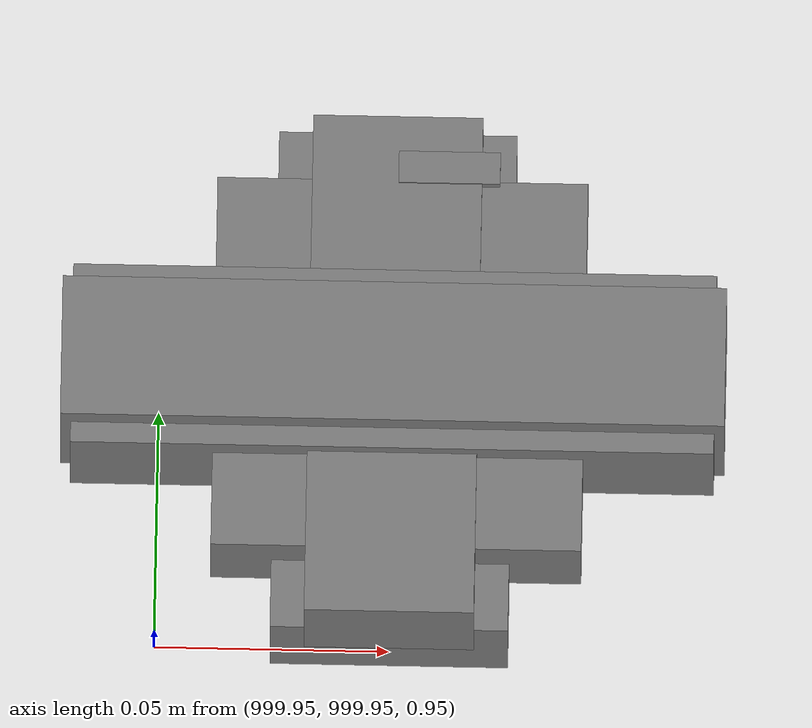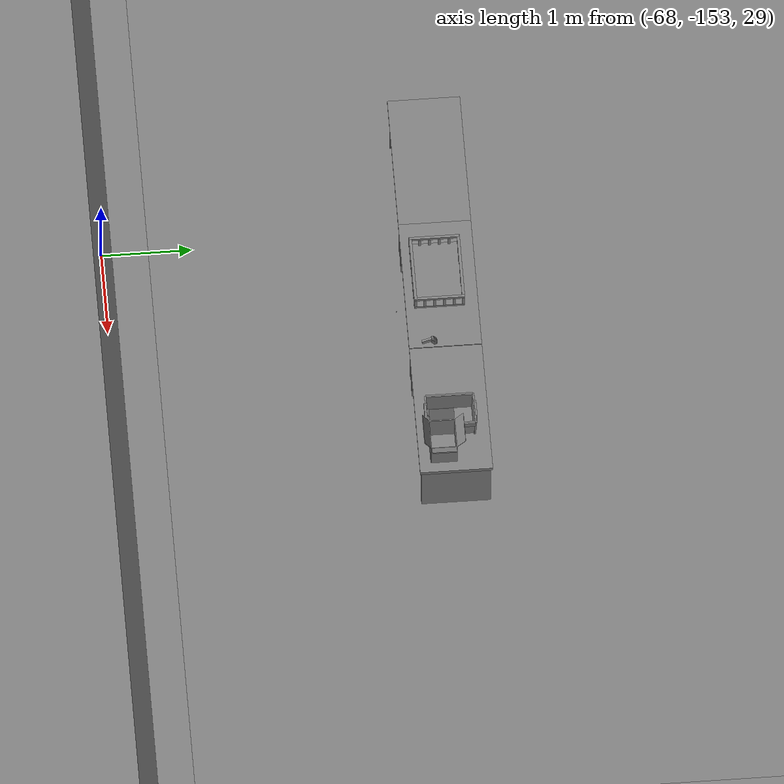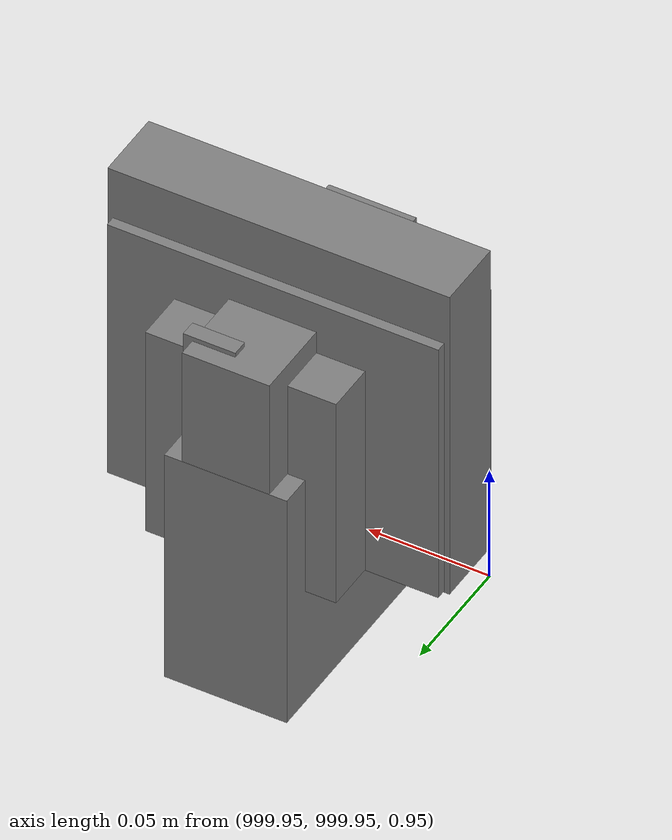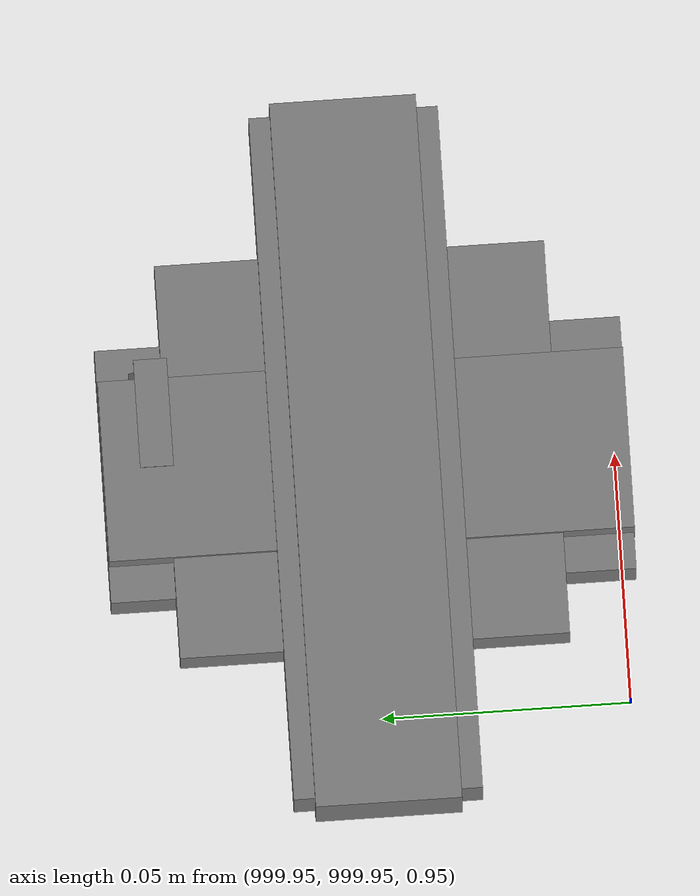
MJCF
<mujoco>
    <option gravity="0.000000000 0.000000000 -9.810000420" timestep="0.0049999999" integrator="implicitfast" density="1.225" viscosity="1.8000001e-05" noslip_iterations="10" iterations="100" sdf_iterations="50">
        <flag multiccd="disable"/>
    </option>
    <size memory="1000M"/>
    <compiler coordinate="local"/>
    <worldbody>
        <light cutoff="30" pos="0 1 1" dir="0 -1 -2"/>
        <light cutoff="30" pos="0 -1 1" dir="0 1 -2"/>
        <body pos="1000.000000000 1000.000000000 1.000000000" euler="0.000000000 0.000000000 180.000000000" name="openloong_gripper_2f85_fix_base_usda_wifi_box">
            <geom contype="1" conaffinity="1" density="1000" type="box" material="" rgba="0.500000000 0.500000000 0.500000000 1.000000000" solimp="0.899999976 0.949999988 0.001000000" friction="1.000000000 0.005000000 0.000100000" solref="0.020000000 1.000000000" margin="0" condim="3" group="0" pos="0.000000000 0.000000000 0.058978677" quat="0.000000000 0.000000047 0.000000000 1.000000000" size="0.068499997 0.018999999 0.059000000" name="openloong_gripper_2f85_fix_base_usda_geom_BD35DBDC_33EF_4EF2_94A3_6B3A1CE1E655"/>
            <freejoint name="openloong_gripper_2f85_fix_base_usda_wifi_box_joint"/>
            <site size="0.005000000 0.005000000 0.005000000" rgba="0.500000000 0.500000000 0.500000000 1.000000000" pos="0.000000000 0.000000000 0.000000000" quat="0.999961913 0.008726500 0.000000000 0.000000000" group="0" type="sphere" name="openloong_gripper_2f85_fix_base_usda_wifi_boxsite"/>
        </body>
        <body pos="1000.000000000 1000.000000000 1.000000000" euler="0.000000000 0.000000000 180.000000000" name="openloong_gripper_2f85_fix_base_usda_cpu_fan">
            <geom contype="1" conaffinity="1" density="1000" type="box" material="" rgba="0.500000000 0.500000000 0.500000000 1.000000000" solimp="0.899999976 0.949999988 0.001000000" friction="1.000000000 0.005000000 0.000100000" solref="0.020000000 1.000000000" margin="0" condim="3" group="0" pos="0.000000000 0.000000000 0.070034981" quat="0.000000000 0.000000000 0.000000000 1.000000000" size="0.070700005 0.014699999 0.070700005" name="openloong_gripper_2f85_fix_base_usda_geom_C134F25B_4786_4D44_9861_5AA0C07913F7"/>
            <freejoint name="openloong_gripper_2f85_fix_base_usda_cpu_fan_joint"/>
            <site size="0.005000000 0.005000000 0.005000000" rgba="0.500000000 0.500000000 0.500000000 1.000000000" pos="0.000000000 0.000000000 0.000000000" quat="0.999961913 0.008726535 0.000000000 0.000000000" group="0" type="sphere" name="openloong_gripper_2f85_fix_base_usda_cpu_fancsite"/>
        </body>
        <body pos="1000.000000000 1000.000000000 1.000000000" euler="0.000000000 0.000000000 180.000000000" name="openloong_gripper_2f85_fix_base_usda_battery_01">
            <geom contype="1" conaffinity="1" density="1000" type="box" material="" rgba="0.500000000 0.500000000 0.500000000 1.000000000" solimp="0.899999976 0.949999988 0.001000000" friction="1.000000000 0.005000000 0.000100000" solref="0.020000000 1.000000000" margin="0" condim="3" group="0" pos="-0.011123657 -0.041940309 0.101691343" quat="1.000000000 0.000000000 0.000000000 0.000000000" size="0.010800000 0.003375000 0.004725000" name="openloong_gripper_2f85_fix_base_usda_geom_188E2B55_808D_4EC5_9E19_1C0FC5096A49"/>
            <geom contype="1" conaffinity="1" density="1000" type="box" material="" rgba="0.500000000 0.500000000 0.500000000 1.000000000" solimp="0.899999976 0.949999988 0.001000000" friction="1.000000000 0.005000000 0.000100000" solref="0.020000000 1.000000000" margin="0" condim="3" group="0" pos="-0.010876465 -0.044247437 0.047066893" quat="0.998702705 -0.050920475 0.000000000 0.000000000" size="0.009450001 0.002700000 0.024975000" name="openloong_gripper_2f85_fix_base_usda_geom_F3E7D4FD_73A7_40A1_BE2A_15D638BCDC48"/>
            <geom contype="1" conaffinity="1" density="1000" type="box" material="" rgba="0.500000000 0.500000000 0.500000000 1.000000000" solimp="0.899999976 0.949999988 0.001000000" friction="1.000000000 0.005000000 0.000100000" solref="0.020000000 1.000000000" margin="0" condim="3" group="0" pos="-0.001235962 -0.000659180 0.047381196" quat="1.000000000 0.000000000 0.000000000 0.000000000" size="0.039420001 0.039150000 0.047250003" name="openloong_gripper_2f85_fix_base_usda_geom_CB87E64C_5BDE_4B05_8DD1_061AA67DF66D"/>
            <geom contype="1" conaffinity="1" density="1000" type="box" material="" rgba="0.500000000 0.500000000 0.500000000 1.000000000" solimp="0.899999976 0.949999988 0.001000000" friction="1.000000000 0.005000000 0.000100000" solref="0.020000000 1.000000000" margin="0" condim="3" group="0" pos="-0.010876465 -0.039138794 0.009851727" quat="1.000000000 0.000000000 0.000000000 0.000000000" size="0.009450001 0.010800000 0.013500000" name="openloong_gripper_2f85_fix_base_usda_geom_41BAD027_203A_4326_A7E5_639E9FD194EE"/>
            <geom contype="1" conaffinity="1" density="1000" type="box" material="" rgba="0.500000000 0.500000000 0.500000000 1.000000000" solimp="0.899999976 0.949999988 0.001000000" friction="1.000000000 0.005000000 0.000100000" solref="0.020000000 1.000000000" margin="0" condim="3" group="0" pos="-0.010876465 -0.041528322 0.071508206" quat="1.000000000 0.000000000 0.000000000 0.000000000" size="0.009450001 0.002700000 0.027000001" name="openloong_gripper_2f85_fix_base_usda_geom_36ECFA01_FD8D_4D88_8ED0_06C901A43BDF"/>
            <freejoint name="openloong_gripper_2f85_fix_base_usda_battery_01_joint"/>
            <site size="0.005000000 0.005000000 0.005000000" rgba="0.500000000 0.500000000 0.500000000 1.000000000" pos="0.000000000 0.000000000 0.000000000" quat="0.999961913 0.008726500 0.000000000 0.000000000" group="0" type="sphere" name="openloong_gripper_2f85_fix_base_usda_battery_01site"/>
        </body>
        <body pos="-66.389930725 -149.442565918 31.163270950" euler="-13.416220665 -84.787460327 -66.669586182" mocap="true" name="spotlight1_SpotLight"/>
        <body pos="-66.143257141 -149.568008423 31.170049667" euler="158.946823120 -0.577833533 84.455680847" mocap="true" name="spotlight6_SpotLight"/>
        <body pos="1000.000000000 1000.000000000 1.000000000" euler="0.000011953 0.000005123 -179.999984741" name="openloong_gripper_2f85_fix_base_usda_intel_box">
            <geom contype="1" conaffinity="1" density="1000" type="box" material="" rgba="0.500000000 0.500000000 0.500000000 1.000000000" solimp="0.899999976 0.949999988 0.001000000" friction="1.000000000 0.005000000 0.000100000" solref="0.020000000 1.000000000" margin="0" condim="3" group="0" pos="0.000000000 -0.000067139 0.000082284" quat="0.707106709 0.000000225 0.000000253 0.707106650" size="0.052800003 0.025300000 0.052800003" name="openloong_gripper_2f85_fix_base_usda_geom_7D1A5AE0_F30E_40D8_88F7_D701E97F8B27"/>
            <freejoint name="openloong_gripper_2f85_fix_base_usda_intel_box_joint"/>
            <site size="0.005000000 0.005000000 0.005000000" rgba="0.500000000 0.500000000 0.500000000 1.000000000" pos="0.000000000 0.000000000 0.000000000" quat="0.999961913 0.008726500 0.000000000 0.000000000" group="0" type="sphere" name="openloong_gripper_2f85_fix_base_usda_intel_boxsite"/>
        </body>
        <body pos="-65.822891235 -149.368148804 31.162452698" euler="-34.194526672 27.550388336 -108.439941406" mocap="true" name="spotlight5_SpotLight"/>
        <body pos="1000.000000000 999.999938965 1.000000000" euler="0.000000000 0.000000000 180.000000000" name="openloong_gripper_2f85_fix_base_usda_intelcore_i5">
            <geom contype="1" conaffinity="1" density="1000" type="box" material="" rgba="0.500000000 0.500000000 0.500000000 1.000000000" solimp="0.899999976 0.949999988 0.001000000" friction="1.000000000 0.005000000 0.000100000" solref="0.020000000 1.000000000" margin="0" condim="3" group="0" pos="0.000000000 0.000000000 0.051722717" quat="0.707106709 0.000000000 0.000000000 -0.707106769" size="0.052800000 0.018080002 0.052800000" name="openloong_gripper_2f85_fix_base_usda_geom_7F836470_C322_472A_85A2_D8BF7A4837E6"/>
            <freejoint name="openloong_gripper_2f85_fix_base_usda_intelcore_i5_joint"/>
            <site size="0.005000000 0.005000000 0.005000000" rgba="0.500000000 0.500000000 0.500000000 1.000000000" pos="0.000000000 0.000000000 0.000000000" quat="0.999961913 0.008726534 0.000000000 0.000000000" group="0" type="sphere" name="openloong_gripper_2f85_fix_base_usda_intelcore_i5site"/>
        </body>
        <body pos="-64.866622925 -149.383972168 30.183746338" euler="89.999984741 89.999946594 0.000000000" name="openloong_gripper_2f85_fix_base_usda_bluebox_01">
            <geom contype="1" conaffinity="1" density="1000" type="box" material="" rgba="0.500000000 0.500000000 0.500000000 1.000000000" solimp="0.899999976 0.949999988 0.001000000" friction="1.000000000 0.005000000 0.000100000" solref="0.020000000 1.000000000" margin="0" condim="3" group="0" pos="0.276580811 0.187225342 0.000068665" quat="0.707106948 0.000077471 0.707106352 0.000077486" size="0.100000001 0.057999998 0.010000000" name="openloong_gripper_2f85_fix_base_usda_geom_197018B5_8450_4312_A73F_3F5EEFD691D3"/>
            <geom contype="1" conaffinity="1" density="1000" type="box" material="" rgba="0.500000000 0.500000000 0.500000000 1.000000000" solimp="0.899999976 0.949999988 0.001000000" friction="1.000000000 0.005000000 0.000100000" solref="0.020000000 1.000000000" margin="0" condim="3" group="0" pos="0.000000000 0.002883911 0.000000000" quat="0.999999881 0.000000000 0.000000000 0.000000000" size="0.254000008 0.003000000 0.172000006" name="openloong_gripper_2f85_fix_base_usda_geom_7F134E8B_17F2_4209_901A_E175041B8037"/>
            <geom contype="1" conaffinity="1" density="1000" type="box" material="" rgba="0.500000000 0.500000000 0.500000000 1.000000000" solimp="0.899999976 0.949999988 0.001000000" friction="1.000000000 0.005000000 0.000100000" solref="0.020000000 1.000000000" margin="0" condim="3" group="0" pos="0.000000000 0.124874115 0.173484802" quat="0.999796331 0.020176515 -0.000000015 0.000000030" size="0.259999990 0.119999997 0.007000000" name="openloong_gripper_2f85_fix_base_usda_geom_5DB421CD_E491_4774_8F4E_D7CC0FD11413"/>
            <geom contype="1" conaffinity="1" density="1000" type="box" material="" rgba="0.500000000 0.500000000 0.500000000 1.000000000" solimp="0.899999976 0.949999988 0.001000000" friction="1.000000000 0.005000000 0.000100000" solref="0.020000000 1.000000000" margin="0" condim="3" group="0" pos="0.000000000 0.124874115 -0.173469543" quat="0.999796331 -0.020176545 -0.000000015 0.000000000" size="0.259999990 0.119999997 0.007000000" name="openloong_gripper_2f85_fix_base_usda_geom_CB91A81B_D9AA_4AA7_9755_ED6279944540"/>
            <geom contype="1" conaffinity="1" density="1000" type="box" material="" rgba="0.500000000 0.500000000 0.500000000 1.000000000" solimp="0.899999976 0.949999988 0.001000000" friction="1.000000000 0.005000000 0.000100000" solref="0.020000000 1.000000000" margin="0" condim="3" group="0" pos="0.000000000 0.214008331 0.188980103" quat="0.999912977 0.013176724 0.000000015 0.000000000" size="0.259999990 0.029999999 0.012500000" name="openloong_gripper_2f85_fix_base_usda_geom_954D9A6E_1856_4103_8F6D_1F856AD74E75"/>
            <geom contype="1" conaffinity="1" density="1000" type="box" material="" rgba="0.500000000 0.500000000 0.500000000 1.000000000" solimp="0.899999976 0.949999988 0.001000000" friction="1.000000000 0.005000000 0.000100000" solref="0.020000000 1.000000000" margin="0" condim="3" group="0" pos="-0.258361816 0.125289917 0.001876831" quat="0.702796936 -0.020792112 0.710783124 0.020769298" size="0.189999998 0.119999997 0.009000000" name="openloong_gripper_2f85_fix_base_usda_geom_691D8E4C_D53B_42B4_802E_113A3894257E"/>
            <geom contype="1" conaffinity="1" density="1000" type="box" material="" rgba="0.500000000 0.500000000 0.500000000 1.000000000" solimp="0.899999976 0.949999988 0.001000000" friction="1.000000000 0.005000000 0.000100000" solref="0.020000000 1.000000000" margin="0" condim="3" group="0" pos="0.000000000 0.214008331 -0.188980103" quat="0.999912977 -0.013176769 0.000000030 0.000000015" size="0.259999990 0.029999999 0.012500000" name="openloong_gripper_2f85_fix_base_usda_geom_A0AB1431_801C_4576_9534_D89120D47DD7"/>
            <geom contype="1" conaffinity="1" density="1000" type="box" material="" rgba="0.500000000 0.500000000 0.500000000 1.000000000" solimp="0.899999976 0.949999988 0.001000000" friction="1.000000000 0.005000000 0.000100000" solref="0.020000000 1.000000000" margin="0" condim="3" group="0" pos="-0.276611328 0.187225342 0.000068665" quat="0.707106650 0.000077441 0.707106709 0.000077456" size="0.100000001 0.057999998 0.010000000" name="openloong_gripper_2f85_fix_base_usda_geom_21ED59E2_0108_46C3_B269_621A0BE0D834"/>
            <geom contype="1" conaffinity="1" density="1000" type="box" material="" rgba="0.500000000 0.500000000 0.500000000 1.000000000" solimp="0.899999976 0.949999988 0.001000000" friction="1.000000000 0.005000000 0.000100000" solref="0.020000000 1.000000000" margin="0" condim="3" group="0" pos="0.258331299 0.125289917 0.001876831" quat="0.702851415 0.018856421 0.710823774 -0.019329369" size="0.189999998 0.119999997 0.009000000" name="openloong_gripper_2f85_fix_base_usda_geom_6AED86ED_E80F_44EC_B4D2_97F4639D7233"/>
            <freejoint name="openloong_gripper_2f85_fix_base_usda_bluebox_01_joint"/>
            <site size="0.005000000 0.005000000 0.005000000" rgba="0.500000000 0.500000000 0.500000000 1.000000000" pos="0.000000000 0.000000000 0.000000000" quat="0.999961913 0.008726534 0.000000000 0.000000000" group="0" type="sphere" name="openloong_gripper_2f85_fix_base_usda_bluebox_01site"/>
        </body>
        <body pos="-64.496299744 -149.491867065 30.235729218" euler="0.000000000 0.000000000 89.999946594" name="openloong_gripper_2f85_fix_base_usda_cardboardbox_01">
            <geom contype="1" conaffinity="1" density="1000" type="box" material="" rgba="0.500000000 0.500000000 0.500000000 1.000000000" solimp="0.899999976 0.949999988 0.001000000" friction="1.000000000 0.005000000 0.000100000" solref="0.020000000 1.000000000" margin="0" condim="3" group="0" pos="-0.003166199 -0.004086494 0.005052090" quat="1.000000000 0.000000000 0.000000000 0.000000000" size="0.142499998 0.177500010 0.005000000" name="openloong_gripper_2f85_fix_base_usda_geom_CA7C11B1_4428_4AF3_85D0_CC89D6C7834C"/>
            <geom contype="1" conaffinity="1" density="1000" type="box" material="" rgba="0.500000000 0.500000000 0.500000000 1.000000000" solimp="0.899999976 0.949999988 0.001000000" friction="1.000000000 0.005000000 0.000100000" solref="0.020000000 1.000000000" margin="0" condim="3" group="0" pos="-0.003166199 0.170316696 0.150570869" quat="1.000000000 0.000000000 0.000000000 0.000000000" size="0.142499998 0.005000000 0.149999991" name="openloong_gripper_2f85_fix_base_usda_geom_B83722D5_91A2_45AC_97FE_AC09CA7515E2"/>
            <geom contype="1" conaffinity="1" density="1000" type="box" material="" rgba="0.500000000 0.500000000 0.500000000 1.000000000" solimp="0.899999976 0.949999988 0.001000000" friction="1.000000000 0.005000000 0.000100000" solref="0.020000000 1.000000000" margin="0" condim="3" group="0" pos="-0.147399902 -0.005307198 0.150570869" quat="1.000000000 0.000000000 0.000000000 0.000000000" size="0.005000000 0.177500010 0.149999991" name="openloong_gripper_2f85_fix_base_usda_geom_A37C88B8_D040_48A5_820A_0CA5B448CE6A"/>
            <geom contype="1" conaffinity="1" density="1000" type="box" material="" rgba="0.500000000 0.500000000 0.500000000 1.000000000" solimp="0.899999976 0.949999988 0.001000000" friction="1.000000000 0.005000000 0.000100000" solref="0.020000000 1.000000000" margin="0" condim="3" group="0" pos="0.140275955 -0.005307198 0.150570869" quat="1.000000000 0.000000000 0.000000000 0.000000000" size="0.005000000 0.177500010 0.149999991" name="openloong_gripper_2f85_fix_base_usda_geom_B4AC4D1A_8B4B_4954_8D69_85564B4E6713"/>
            <geom contype="1" conaffinity="1" density="1000" type="box" material="" rgba="0.500000000 0.500000000 0.500000000 1.000000000" solimp="0.899999976 0.949999988 0.001000000" friction="1.000000000 0.005000000 0.000100000" solref="0.020000000 1.000000000" margin="0" condim="3" group="0" pos="-0.003166199 -0.181550980 0.150570869" quat="1.000000000 0.000000000 0.000000000 0.000000000" size="0.142499998 0.005000000 0.149999991" name="openloong_gripper_2f85_fix_base_usda_geom_6AD5294A_A91B_49C1_8ED7_97AC7629D4D4"/>
            <freejoint name="openloong_gripper_2f85_fix_base_usda_cardboardbox_01_joint"/>
            <site size="0.005000000 0.005000000 0.005000000" rgba="0.500000000 0.500000000 0.500000000 1.000000000" pos="0.000000000 0.000000000 0.000000000" quat="0.999961913 0.008726535 0.000000000 0.000000000" group="0" type="sphere" name="openloong_gripper_2f85_fix_base_usda_site_D6BECB94_1E03_460E_A6BD_988172B5B4E9"/>
            <body pos="0.139160156 -0.004048347 0.301930904" euler="-179.999954224 49.383502960 179.999954224" name="openloong_gripper_2f85_fix_base_usda_A1_006">
                <geom contype="1" conaffinity="1" density="1000" type="box" material="" rgba="0.500000000 0.500000000 0.500000000 1.000000000" solimp="0.899999976 0.949999988 0.001000000" friction="1.000000000 0.005000000 0.000100000" solref="0.020000000 1.000000000" margin="0" condim="3" group="0" pos="-0.071587563 0.000009537 0.001745224" quat="0.999999881 0.000000000 0.000000000 0.000000000" size="0.071249999 0.179999992 0.002500000" name="openloong_gripper_2f85_fix_base_usda_geom_EA7C9DBF_7C41_40D5_9A41_10314FD133F5"/>
                <joint armature="0" stiffness="0.07" damping="0.0099999998" axis="0.000000 1.000000 0.000000" type="hinge" name="openloong_gripper_2f85_fix_base_usda_A1_006"/>
            </body>
            <body pos="-0.145902634 -0.004086494 0.301938057" euler="-180.000000000 -60.000011444 -180.000000000" name="openloong_gripper_2f85_fix_base_usda_A2_006">
                <geom contype="1" conaffinity="1" density="1000" type="box" material="" rgba="0.500000000 0.500000000 0.500000000 1.000000000" solimp="0.899999976 0.949999988 0.001000000" friction="1.000000000 0.005000000 0.000100000" solref="0.020000000 1.000000000" margin="0" condim="3" group="0" pos="0.071268082 0.000009537 0.002717972" quat="0.000002921 0.000000000 -0.000000030 0.999999881" size="0.071249999 0.179999992 0.002500000" name="openloong_gripper_2f85_fix_base_usda_geom_8F9090BE_F352_42FA_A6FA_108BD5219696"/>
                <joint armature="0" stiffness="0.07" damping="0.0099999998" axis="0.000000 1.000000 0.000000" type="hinge" name="openloong_gripper_2f85_fix_base_usda_A2_006"/>
            </body>
            <body pos="-0.003385544 0.175991058 0.301930904" euler="-125.858116150 -0.000004561 0.000002331" name="openloong_gripper_2f85_fix_base_usda_B2_006">
                <geom contype="1" conaffinity="1" density="1000" type="box" material="" rgba="0.500000000 0.500000000 0.500000000 1.000000000" solimp="0.899999976 0.949999988 0.001000000" friction="1.000000000 0.005000000 0.000100000" solref="0.020000000 1.000000000" margin="0" condim="3" group="0" pos="0.000009537 -0.070939064 -0.002470016" quat="0.999614120 0.027776197 -0.000000015 0.000000030" size="0.137500003 0.064999998 0.005000000" name="openloong_gripper_2f85_fix_base_usda_geom_715DD693_5A78_4BA6_BA6B_AA276EA8FE74"/>
                <joint armature="0" stiffness="0.07" damping="0.0099999998" axis="1.000000 0.000000 0.000000" type="hinge" name="openloong_gripper_2f85_fix_base_usda_B2_006"/>
            </body>
            <body pos="-0.003385544 -0.184140205 0.301938057" euler="147.805557251 0.000000000 0.000000000" name="openloong_gripper_2f85_fix_base_usda_B1_006">
                <geom contype="1" conaffinity="1" density="1000" type="box" material="" rgba="0.500000000 0.500000000 0.500000000 1.000000000" solimp="0.899999976 0.949999988 0.001000000" friction="1.000000000 0.005000000 0.000100000" solref="0.020000000 1.000000000" margin="0" condim="3" group="0" pos="-0.000028610 0.070202351 -0.002703667" quat="0.999614179 -0.027776167 0.000000000 0.000000000" size="0.137500003 0.064999998 0.005000000" name="openloong_gripper_2f85_fix_base_usda_geom_03608B5B_CB29_4810_A2EC_8FF58BCC55E3"/>
                <joint armature="0" stiffness="0.07" damping="0.0099999998" axis="1.000000 0.000000 0.000000" type="hinge" name="openloong_gripper_2f85_fix_base_usda_B1_006"/>
            </body>
        </body>
        <body pos="-65.882858276 -149.481979370 30.229999542" euler="-64.487716675 0.000000000 0.000000000" name="openloong_gripper_2f85_fix_base_usda_Barcode">
            <geom contype="1" conaffinity="1" density="1000" type="box" material="" rgba="0.500000000 0.500000000 0.500000000 1.000000000" solimp="0.899999976 0.949999988 0.001000000" friction="1.000000000 0.005000000 0.000100000" solref="0.020000000 1.000000000" margin="0" condim="3" group="0" pos="0.000000000 0.013038635 0.001419067" quat="0.000000000 0.000000000 0.000000000 1.000000119" size="0.034000002 0.010000000 0.017999999" name="openloong_gripper_2f85_fix_base_usda_geom_7DAEC68D_D6C3_41AE_ADCC_6AB44AA8E6BF"/>
            <geom contype="1" conaffinity="1" density="1000" type="box" material="" rgba="0.500000000 0.500000000 0.500000000 1.000000000" solimp="0.899999976 0.949999988 0.001000000" friction="1.000000000 0.005000000 0.000100000" solref="0.020000000 1.000000000" margin="0" condim="3" group="0" pos="0.000000000 -0.035301208 -0.007095337" quat="0.000000000 0.000000000 -0.043619365 0.999048233" size="0.028999999 0.010000000 0.020000000" name="openloong_gripper_2f85_fix_base_usda_geom_EFA6B5D3_EE9F_47A4_B3C6_F2FB8CBCDED8"/>
            <geom contype="1" conaffinity="1" density="1000" type="box" material="" rgba="0.500000000 0.500000000 0.500000000 1.000000000" solimp="0.899999976 0.949999988 0.001000000" friction="1.000000000 0.005000000 0.000100000" solref="0.020000000 1.000000000" margin="0" condim="3" group="0" pos="0.000000000 -0.043411255 -0.011749268" quat="0.922262907 0.386563420 0.000000000 0.000000000" size="0.026000001 0.010000000 0.020000000" name="openloong_gripper_2f85_fix_base_usda_geom_7D3F3531_D71D_4367_97B8_1B95A50E0CE4"/>
            <geom contype="1" conaffinity="1" density="1000" type="box" material="" rgba="0.500000000 0.500000000 0.500000000 1.000000000" solimp="0.899999976 0.949999988 0.001000000" friction="1.000000000 0.005000000 0.000100000" solref="0.020000000 1.000000000" margin="0" condim="3" group="0" pos="0.000000000 -0.016967773 -0.031860352" quat="0.000000000 0.000000000 0.000000000 1.000000119" size="0.008000000 0.010000000 0.013000000" name="openloong_gripper_2f85_fix_base_usda_geom_658B3150_AB47_49B4_BC88_278EAFCC70D8"/>
            <geom contype="1" conaffinity="1" density="1000" type="box" material="" rgba="0.500000000 0.500000000 0.500000000 1.000000000" solimp="0.899999976 0.949999988 0.001000000" friction="1.000000000 0.005000000 0.000100000" solref="0.020000000 1.000000000" margin="0" condim="3" group="0" pos="0.000000000 -0.001869202 0.000312805" quat="0.953716993 0.300705761 0.000000000 0.000000000" size="0.032000002 0.010000000 0.018999999" name="openloong_gripper_2f85_fix_base_usda_geom_06540952_93D2_42C6_8785_A7E4DBBB63B5"/>
            <geom contype="1" conaffinity="1" density="1000" type="box" material="" rgba="0.500000000 0.500000000 0.500000000 1.000000000" solimp="0.899999976 0.949999988 0.001000000" friction="1.000000000 0.005000000 0.000100000" solref="0.020000000 1.000000000" margin="0" condim="3" group="0" pos="0.000000000 -0.019531250 -0.003173828" quat="0.953716993 0.300705761 0.000000000 0.000000000" size="0.030999999 0.010000000 0.020000000" name="openloong_gripper_2f85_fix_base_usda_geom_E2362960_A942_4A37_9B0B_29BC48249A80"/>
            <geom contype="1" conaffinity="1" density="1000" type="box" material="" rgba="0.500000000 0.500000000 0.500000000 1.000000000" solimp="0.899999976 0.949999988 0.001000000" friction="1.000000000 0.005000000 0.000100000" solref="0.020000000 1.000000000" margin="0" condim="3" group="0" pos="0.000000000 -0.035301208 -0.007095337" quat="0.953716993 0.300705761 0.000000000 0.000000000" size="0.028999999 0.010000000 0.020000000" name="openloong_gripper_2f85_fix_base_usda_geom_1D6CB7E6_34DC_4103_BF67_6F3CA61BDA6A"/>
            <geom contype="1" conaffinity="1" density="1000" type="box" material="" rgba="0.500000000 0.500000000 0.500000000 1.000000000" solimp="0.899999976 0.949999988 0.001000000" friction="1.000000000 0.005000000 0.000100000" solref="0.020000000 1.000000000" margin="0" condim="3" group="0" pos="0.000000000 -0.042617798 -0.071121216" quat="0.000000000 0.000000000 0.000000000 1.000000119" size="0.013000000 0.021000000 0.059999999" name="openloong_gripper_2f85_fix_base_usda_geom_5D8FA6AA_4CE5_4FEB_9B5A_300A30C84552"/>
            <freejoint name="openloong_gripper_2f85_fix_base_usda_Barcode_joint"/>
            <site size="0.005000000 0.005000000 0.005000000" rgba="0.500000000 0.500000000 0.500000000 1.000000000" pos="0.000000000 0.000000000 0.000000000" quat="1.000000000 0.000000000 0.000000000 0.000000000" group="0" type="sphere" name="openloong_gripper_2f85_fix_base_usda_Barcode_site"/>
        </body>
        <body pos="-66.745018005 -149.392349243 30.184000015" euler="0.000000000 0.000000000 89.999946594" name="[22330123540185]_Basket_01">
            <geom contype="1" conaffinity="1" density="1000" type="box" material="" rgba="0.500000000 0.500000000 0.500000000 1.000000000" solimp="0.899999976 0.949999988 0.001000000" friction="1.000000000 0.005000000 0.000100000" solref="0.020000000 1.000000000" margin="0" condim="3" group="0" pos="-0.052425385 0.389207840 0.089787483" quat="0.707107008 0.000000000 0.000000000 0.707106411" size="0.014249999 0.014249999 0.059999999" name="[22330123540185]_geom_F76619F1_BDAA_481A_B659_44E72DEF359D"/>
            <geom contype="1" conaffinity="1" density="1000" type="box" material="" rgba="0.500000000 0.500000000 0.500000000 1.000000000" solimp="0.899999976 0.949999988 0.001000000" friction="1.000000000 0.005000000 0.000100000" solref="0.020000000 1.000000000" margin="0" condim="3" group="0" pos="0.264015198 -0.133043289 0.089787483" quat="0.707107008 0.000000000 0.000000000 0.707106411" size="0.014249999 0.014249999 0.059999999" name="[22330123540185]_geom_6F8CAC21_7DD4_4428_B98B_A1884BC610C1"/>
            <geom contype="1" conaffinity="1" density="1000" type="box" material="" rgba="0.500000000 0.500000000 0.500000000 1.000000000" solimp="0.899999976 0.949999988 0.001000000" friction="1.000000000 0.005000000 0.000100000" solref="0.020000000 1.000000000" margin="0" condim="3" group="0" pos="-0.264015198 -0.265548706 0.089793205" quat="0.707107008 0.000000000 0.000000000 0.707106411" size="0.014249999 0.014249999 0.059999999" name="[22330123540185]_geom_2D48D928_3B53_433C_B14D_27FFD40FFCFF"/>
            <geom contype="1" conaffinity="1" density="1000" type="box" material="" rgba="0.500000000 0.500000000 0.500000000 1.000000000" solimp="0.899999976 0.949999988 0.001000000" friction="1.000000000 0.005000000 0.000100000" solref="0.020000000 1.000000000" margin="0" condim="3" group="0" pos="-0.160263062 -0.389322281 0.089793205" quat="0.707107008 0.000000000 0.000000000 0.707106411" size="0.014249999 0.014249999 0.059999999" name="[22330123540185]_geom_DE04D7F9_F385_4A14_B30F_094741743992"/>
            <geom contype="1" conaffinity="1" density="1000" type="box" material="" rgba="0.500000000 0.500000000 0.500000000 1.000000000" solimp="0.899999976 0.949999988 0.001000000" friction="1.000000000 0.005000000 0.000100000" solref="0.020000000 1.000000000" margin="0" condim="3" group="0" pos="0.162265778 -0.389322281 0.089787483" quat="0.707107008 0.000000000 0.000000000 0.707106411" size="0.014249999 0.014249999 0.059999999" name="[22330123540185]_geom_7373E8DA_81A9_4FE2_BD89_D2B8E7DDDD90"/>
            <geom contype="1" conaffinity="1" density="1000" type="box" material="" rgba="0.500000000 0.500000000 0.500000000 1.000000000" solimp="0.899999976 0.949999988 0.001000000" friction="1.000000000 0.005000000 0.000100000" solref="0.020000000 1.000000000" margin="0" condim="3" group="0" pos="0.264015198 0.389207840 0.089787483" quat="0.707107008 0.000000000 0.000000000 0.707106411" size="0.014249999 0.014249999 0.059999999" name="[22330123540185]_geom_CFC41CDB_9970_4898_84B7_F93507B6D784"/>
            <geom contype="1" conaffinity="1" density="1000" type="box" material="" rgba="0.500000000 0.500000000 0.500000000 1.000000000" solimp="0.899999976 0.949999988 0.001000000" friction="1.000000000 0.005000000 0.000100000" solref="0.020000000 1.000000000" margin="0" condim="3" group="0" pos="-0.264015198 -0.133043289 0.089793205" quat="0.707107008 0.000000000 0.000000000 0.707106411" size="0.014249999 0.014249999 0.059999999" name="[22330123540185]_geom_947F6252_673D_4F13_99D3_BA055CA4F9CD"/>
            <geom contype="1" conaffinity="1" density="1000" type="box" material="" rgba="0.500000000 0.500000000 0.500000000 1.000000000" solimp="0.899999976 0.949999988 0.001000000" friction="1.000000000 0.005000000 0.000100000" solref="0.020000000 1.000000000" margin="0" condim="3" group="0" pos="-0.264026642 0.269256592 0.089793205" quat="0.707107008 0.000000000 0.000000000 0.707106411" size="0.014249999 0.014249999 0.059999999" name="[22330123540185]_geom_FCA7D8EB_DD55_4D3A_B6B5_E4F7A364FEFD"/>
            <geom contype="1" conaffinity="1" density="1000" type="box" material="" rgba="0.500000000 0.500000000 0.500000000 1.000000000" solimp="0.899999976 0.949999988 0.001000000" friction="1.000000000 0.005000000 0.000100000" solref="0.020000000 1.000000000" margin="0" condim="3" group="0" pos="0.054462433 0.389207840 0.089787483" quat="0.707107008 0.000000000 0.000000000 0.707106411" size="0.014249999 0.014249999 0.059999999" name="[22330123540185]_geom_6118F175_6CF4_4F0E_8924_EC063E5D6358"/>
            <geom contype="1" conaffinity="1" density="1000" type="box" material="" rgba="0.500000000 0.500000000 0.500000000 1.000000000" solimp="0.899999976 0.949999988 0.001000000" friction="1.000000000 0.005000000 0.000100000" solref="0.020000000 1.000000000" margin="0" condim="3" group="0" pos="0.054462433 -0.389322281 0.089787483" quat="0.707107008 0.000000000 0.000000000 0.707106411" size="0.014249999 0.014249999 0.059999999" name="[22330123540185]_geom_59323EB4_9B9B_4DE6_8184_9055293A34ED"/>
            <geom contype="1" conaffinity="1" density="1000" type="box" material="" rgba="0.500000000 0.500000000 0.500000000 1.000000000" solimp="0.899999976 0.949999988 0.001000000" friction="1.000000000 0.005000000 0.000100000" solref="0.020000000 1.000000000" margin="0" condim="3" group="0" pos="0.264015198 0.269256592 0.089793205" quat="0.707107008 0.000000000 0.000000000 0.707106411" size="0.014249999 0.014249999 0.059999999" name="[22330123540185]_geom_189916BD_2EA9_4398_955D_EEB5CD5FD9FB"/>
            <geom contype="1" conaffinity="1" density="1000" type="box" material="" rgba="0.500000000 0.500000000 0.500000000 1.000000000" solimp="0.899999976 0.949999988 0.001000000" friction="1.000000000 0.005000000 0.000100000" solref="0.020000000 1.000000000" margin="0" condim="3" group="0" pos="0.264015198 -0.389322281 0.089787483" quat="0.707107008 0.000000000 0.000000000 0.707106411" size="0.014249999 0.014249999 0.059999999" name="[22330123540185]_geom_9EABAF77_968A_4822_8FAC_64F6B507F26A"/>
            <geom contype="1" conaffinity="1" density="1000" type="box" material="" rgba="0.500000000 0.500000000 0.500000000 1.000000000" solimp="0.899999976 0.949999988 0.001000000" friction="1.000000000 0.005000000 0.000100000" solref="0.020000000 1.000000000" margin="0" condim="3" group="0" pos="0.000000000 0.000000000 0.015998840" quat="0.707107008 0.000000000 0.000000000 0.707106411" size="0.403499991 0.279000014 0.015750000" name="[22330123540185]_geom_6116041D_AC2F_4ED2_B505_8367F6E588BA"/>
            <geom contype="1" conaffinity="1" density="1000" type="box" material="" rgba="0.500000000 0.500000000 0.500000000 1.000000000" solimp="0.899999976 0.949999988 0.001000000" friction="1.000000000 0.005000000 0.000100000" solref="0.020000000 1.000000000" margin="0" condim="3" group="0" pos="0.000000000 -0.389476776 0.163619041" quat="0.707107008 0.000000000 0.000000000 0.707106411" size="0.015000000 0.277500004 0.015750000" name="[22330123540185]_geom_96DD7BB0_2959_4BB3_9C97_BE3D85B4EC25"/>
            <geom contype="1" conaffinity="1" density="1000" type="box" material="" rgba="0.500000000 0.500000000 0.500000000 1.000000000" solimp="0.899999976 0.949999988 0.001000000" friction="1.000000000 0.005000000 0.000100000" solref="0.020000000 1.000000000" margin="0" condim="3" group="0" pos="0.162265778 0.389207840 0.089787483" quat="0.707107008 0.000000000 0.000000000 0.707106411" size="0.014249999 0.014249999 0.059999999" name="[22330123540185]_geom_F1A364F3_6520_4B3C_A04D_6BDBA122C35F"/>
            <geom contype="1" conaffinity="1" density="1000" type="box" material="" rgba="0.500000000 0.500000000 0.500000000 1.000000000" solimp="0.899999976 0.949999988 0.001000000" friction="1.000000000 0.005000000 0.000100000" solref="0.020000000 1.000000000" margin="0" condim="3" group="0" pos="0.000000000 0.389471054 0.163619041" quat="0.707107008 0.000000000 0.000000000 0.707106411" size="0.015000000 0.277500004 0.015750000" name="[22330123540185]_geom_359B43CF_31DB_48FC_A1B3_046E39BBC178"/>
            <geom contype="1" conaffinity="1" density="1000" type="box" material="" rgba="0.500000000 0.500000000 0.500000000 1.000000000" solimp="0.899999976 0.949999988 0.001000000" friction="1.000000000 0.005000000 0.000100000" solref="0.020000000 1.000000000" margin="0" condim="3" group="0" pos="-0.263511658 0.000000000 0.163619041" quat="0.707107008 0.000000000 0.000000000 0.707106411" size="0.403499991 0.015000000 0.015750000" name="[22330123540185]_geom_53CF7047_EFAF_4799_9096_F79010000D3A"/>
            <geom contype="1" conaffinity="1" density="1000" type="box" material="" rgba="0.500000000 0.500000000 0.500000000 1.000000000" solimp="0.899999976 0.949999988 0.001000000" friction="1.000000000 0.005000000 0.000100000" solref="0.020000000 1.000000000" margin="0" condim="3" group="0" pos="-0.264015198 0.141334534 0.089793205" quat="0.707107008 0.000000000 0.000000000 0.707106411" size="0.014249999 0.014249999 0.059999999" name="[22330123540185]_geom_180F8D0A_D42F_406C_B62F_C1D0A875CBC8"/>
            <geom contype="1" conaffinity="1" density="1000" type="box" material="" rgba="0.500000000 0.500000000 0.500000000 1.000000000" solimp="0.899999976 0.949999988 0.001000000" friction="1.000000000 0.005000000 0.000100000" solref="0.020000000 1.000000000" margin="0" condim="3" group="0" pos="0.264015198 -0.265548706 0.089787483" quat="0.707107008 0.000000000 0.000000000 0.707106411" size="0.014249999 0.014249999 0.059999999" name="[22330123540185]_geom_E775A1B4_047A_4E94_BD49_E8B26CFD8A93"/>
            <geom contype="1" conaffinity="1" density="1000" type="box" material="" rgba="0.500000000 0.500000000 0.500000000 1.000000000" solimp="0.899999976 0.949999988 0.001000000" friction="1.000000000 0.005000000 0.000100000" solref="0.020000000 1.000000000" margin="0" condim="3" group="0" pos="-0.160263062 0.389207840 0.089787483" quat="0.707107008 0.000000000 0.000000000 0.707106411" size="0.014249999 0.014249999 0.059999999" name="[22330123540185]_geom_AF5652E1_0A5A_401A_990A_2C0624E0F1E8"/>
            <geom contype="1" conaffinity="1" density="1000" type="box" material="" rgba="0.500000000 0.500000000 0.500000000 1.000000000" solimp="0.899999976 0.949999988 0.001000000" friction="1.000000000 0.005000000 0.000100000" solref="0.020000000 1.000000000" margin="0" condim="3" group="0" pos="-0.052425385 -0.389322281 0.089787483" quat="0.707107008 0.000000000 0.000000000 0.707106411" size="0.014249999 0.014249999 0.059999999" name="[22330123540185]_geom_66F2267E_76CB_41D4_B2B7_937DBD11B7C9"/>
            <geom contype="1" conaffinity="1" density="1000" type="box" material="" rgba="0.500000000 0.500000000 0.500000000 1.000000000" solimp="0.899999976 0.949999988 0.001000000" friction="1.000000000 0.005000000 0.000100000" solref="0.020000000 1.000000000" margin="0" condim="3" group="0" pos="-0.264026642 -0.389322281 0.089793205" quat="0.707107008 0.000000000 0.000000000 0.707106411" size="0.014249999 0.014249999 0.059999999" name="[22330123540185]_geom_27D3CEA1_81A0_48C8_933D_057145453679"/>
            <geom contype="1" conaffinity="1" density="1000" type="box" material="" rgba="0.500000000 0.500000000 0.500000000 1.000000000" solimp="0.899999976 0.949999988 0.001000000" friction="1.000000000 0.005000000 0.000100000" solref="0.020000000 1.000000000" margin="0" condim="3" group="0" pos="0.264015198 0.141334534 0.089787483" quat="0.707107008 0.000000000 0.000000000 0.707106411" size="0.014249999 0.014249999 0.059999999" name="[22330123540185]_geom_D152B6A3_33AD_4386_9B7C_A65EBE299074"/>
            <geom contype="1" conaffinity="1" density="1000" type="box" material="" rgba="0.500000000 0.500000000 0.500000000 1.000000000" solimp="0.899999976 0.949999988 0.001000000" friction="1.000000000 0.005000000 0.000100000" solref="0.020000000 1.000000000" margin="0" condim="3" group="0" pos="-0.264015198 0.389207840 0.089793205" quat="0.707107008 0.000000000 0.000000000 0.707106411" size="0.014249999 0.014249999 0.059999999" name="[22330123540185]_geom_6B45E7A9_3032_408D_BB79_C7999FD16CDF"/>
            <geom contype="1" conaffinity="1" density="1000" type="box" material="" rgba="0.500000000 0.500000000 0.500000000 1.000000000" solimp="0.899999976 0.949999988 0.001000000" friction="1.000000000 0.005000000 0.000100000" solref="0.020000000 1.000000000" margin="0" condim="3" group="0" pos="0.264015198 0.004480362 0.089787483" quat="0.707107008 0.000000000 0.000000000 0.707106411" size="0.014249999 0.014249999 0.059999999" name="[22330123540185]_geom_09A888BD_C603_4B93_87B8_1F2DDC936799"/>
            <geom contype="1" conaffinity="1" density="1000" type="box" material="" rgba="0.500000000 0.500000000 0.500000000 1.000000000" solimp="0.899999976 0.949999988 0.001000000" friction="1.000000000 0.005000000 0.000100000" solref="0.020000000 1.000000000" margin="0" condim="3" group="0" pos="0.263694763 -0.000011444 0.163619041" quat="0.707107008 0.000000000 0.000000000 0.707106411" size="0.403499991 0.015000000 0.015750000" name="[22330123540185]_geom_82B288A8_033F_4008_B6C6_0EE9A2EFA611"/>
            <geom contype="1" conaffinity="1" density="1000" type="box" material="" rgba="0.500000000 0.500000000 0.500000000 1.000000000" solimp="0.899999976 0.949999988 0.001000000" friction="1.000000000 0.005000000 0.000100000" solref="0.020000000 1.000000000" margin="0" condim="3" group="0" pos="-0.264015198 0.004480362 0.089793205" quat="0.707107008 0.000000000 0.000000000 0.707106411" size="0.014249999 0.014249999 0.059999999" name="[22330123540185]_geom_7DC610F6_8015_4376_A410_116CFD83BC06"/>
            <freejoint name="[22330123540185]_joint_82419FE6_E963_482C_9698_01F00EAECA73"/>
        </body>
        <body pos="0.000000000 0.000000000 0.000000000" euler="0.000000000 0.000000000 0.000000000" name="Static Objects_Static Objects">
            <geom contype="1" conaffinity="1" density="1000" type="box" material="" rgba="0.500000000 0.500000000 0.500000000 1.000000000" solimp="0.899999976 0.949999988 0.001000000" friction="1.000000000 0.005000000 0.000100000" solref="0.020000000 1.000000000" margin="0" condim="3" group="0" pos="-67.544113159 -149.365814209 29.727830887" quat="0.500000417 0.499999970 0.499999553 0.499999970" size="0.381000012 0.319999993 0.041000001" name="Static Objects_geom_8E863F10_318F_458C_BB90_3DE0A0581E07"/>
            <geom contype="1" conaffinity="1" density="1000" type="box" material="" rgba="0.500000000 0.500000000 0.500000000 1.000000000" solimp="0.899999976 0.949999988 0.001000000" friction="1.000000000 0.005000000 0.000100000" solref="0.020000000 1.000000000" margin="0" condim="3" group="0" pos="-68.239501953 -149.365814209 30.086868286" quat="0.500000417 0.499999970 0.499999553 0.499999970" size="0.370999992 0.039500002 0.745000005" name="Static Objects_geom_7372A528_B7E2_482C_85E1_1BA77DD6DC79"/>
            <geom contype="1" conaffinity="1" density="1000" type="box" material="" rgba="0.500000000 0.500000000 0.500000000 1.000000000" solimp="0.899999976 0.949999988 0.001000000" friction="1.000000000 0.005000000 0.000100000" solref="0.020000000 1.000000000" margin="0" condim="3" group="0" pos="-68.239501953 -149.365814209 30.147235870" quat="0.500000417 0.499999970 0.499999553 0.499999970" size="0.400000006 0.022000000 0.800000012" name="Static Objects_geom_4D893328_2BDA_43D8_BB7A_CED805C707EF"/>
            <geom contype="1" conaffinity="1" density="1000" type="box" material="" rgba="0.500000000 0.500000000 0.500000000 1.000000000" solimp="0.899999976 0.949999988 0.001000000" friction="1.000000000 0.005000000 0.000100000" solref="0.020000000 1.000000000" margin="0" condim="3" group="0" pos="-68.934890747 -149.365814209 29.727830887" quat="0.500000417 0.499999970 0.499999553 0.499999970" size="0.381000012 0.319999993 0.041000001" name="Static Objects_geom_0509C76A_3FCF_41D8_BB72_B46733A40079"/>
            <geom contype="1" conaffinity="1" density="1000" type="box" material="" rgba="0.500000000 0.500000000 0.500000000 1.000000000" solimp="0.899999976 0.949999988 0.001000000" friction="1.000000000 0.005000000 0.000100000" solref="0.020000000 1.000000000" margin="0" condim="3" group="0" pos="-68.239501953 -149.365814209 29.561563492" quat="0.500000417 0.499999970 0.499999553 0.499999970" size="0.020000000 0.022000000 0.660000026" name="Static Objects_geom_CD8AD242_2F92_4C98_8689_C3C188E42A18"/>
            <geom contype="1" conaffinity="1" density="1000" type="box" material="" rgba="0.500000000 0.500000000 0.500000000 1.000000000" solimp="0.899999976 0.949999988 0.001000000" friction="1.000000000 0.005000000 0.000100000" solref="0.020000000 1.000000000" margin="0" condim="3" group="0" pos="-65.945671082 -149.365814209 29.727830887" quat="0.500000417 0.499999970 0.499999553 0.499999970" size="0.381000012 0.319999993 0.041000001" name="Static Objects_geom_CA470D1A_55D5_47BA_9855_2CAE5638A158"/>
            <geom contype="1" conaffinity="1" density="1000" type="box" material="" rgba="0.500000000 0.500000000 0.500000000 1.000000000" solimp="0.899999976 0.949999988 0.001000000" friction="1.000000000 0.005000000 0.000100000" solref="0.020000000 1.000000000" margin="0" condim="3" group="0" pos="-66.641059875 -149.365814209 30.086868286" quat="0.500000417 0.499999970 0.499999553 0.499999970" size="0.370999992 0.039500002 0.745000005" name="Static Objects_geom_53B915B2_0DE6_4D05_877E_5E1257381C55"/>
            <geom contype="1" conaffinity="1" density="1000" type="box" material="" rgba="0.500000000 0.500000000 0.500000000 1.000000000" solimp="0.899999976 0.949999988 0.001000000" friction="1.000000000 0.005000000 0.000100000" solref="0.020000000 1.000000000" margin="0" condim="3" group="0" pos="-66.641059875 -149.365814209 30.147235870" quat="0.500000417 0.499999970 0.499999553 0.499999970" size="0.400000006 0.022000000 0.800000012" name="Static Objects_geom_8F58BACA_5C33_400E_8984_22E7EAD3500B"/>
            <geom contype="1" conaffinity="1" density="1000" type="box" material="" rgba="0.500000000 0.500000000 0.500000000 1.000000000" solimp="0.899999976 0.949999988 0.001000000" friction="1.000000000 0.005000000 0.000100000" solref="0.020000000 1.000000000" margin="0" condim="3" group="0" pos="-67.336448669 -149.365814209 29.727830887" quat="0.500000417 0.499999970 0.499999553 0.499999970" size="0.381000012 0.319999993 0.041000001" name="Static Objects_geom_2F4F29DE_BCE3_44BB_A157_D9E9AECEF7E2"/>
            <geom contype="1" conaffinity="1" density="1000" type="box" material="" rgba="0.500000000 0.500000000 0.500000000 1.000000000" solimp="0.899999976 0.949999988 0.001000000" friction="1.000000000 0.005000000 0.000100000" solref="0.020000000 1.000000000" margin="0" condim="3" group="0" pos="-66.641059875 -149.365814209 29.561563492" quat="0.500000417 0.499999970 0.499999553 0.499999970" size="0.020000000 0.022000000 0.660000026" name="Static Objects_geom_7F3BC709_BECA_47C8_A381_AD3ED17BA51B"/>
            <geom contype="1" conaffinity="1" density="1000" type="box" material="" rgba="0.500000000 0.500000000 0.500000000 1.000000000" solimp="0.899999976 0.949999988 0.001000000" friction="1.000000000 0.005000000 0.000100000" solref="0.020000000 1.000000000" margin="0" condim="3" group="0" pos="-64.338577271 -149.365814209 29.727830887" quat="0.500000417 0.499999970 0.499999553 0.499999970" size="0.381000012 0.319999993 0.041000001" name="Static Objects_geom_040CC65C_D781_486E_A9DC_A800C39731AB"/>
            <geom contype="1" conaffinity="1" density="1000" type="box" material="" rgba="0.500000000 0.500000000 0.500000000 1.000000000" solimp="0.899999976 0.949999988 0.001000000" friction="1.000000000 0.005000000 0.000100000" solref="0.020000000 1.000000000" margin="0" condim="3" group="0" pos="-65.033966064 -149.365814209 30.086868286" quat="0.500000417 0.499999970 0.499999553 0.499999970" size="0.370999992 0.039500002 0.745000005" name="Static Objects_geom_6CF6D7BA_53F5_4DD8_8C59_17ACEBB2F66C"/>
            <geom contype="1" conaffinity="1" density="1000" type="box" material="" rgba="0.500000000 0.500000000 0.500000000 1.000000000" solimp="0.899999976 0.949999988 0.001000000" friction="1.000000000 0.005000000 0.000100000" solref="0.020000000 1.000000000" margin="0" condim="3" group="0" pos="-65.033966064 -149.365814209 30.147235870" quat="0.500000417 0.499999970 0.499999553 0.499999970" size="0.400000006 0.022000000 0.800000012" name="Static Objects_geom_2C4B68C4_0939_4271_B67A_22959A636E18"/>
            <geom contype="1" conaffinity="1" density="1000" type="box" material="" rgba="0.500000000 0.500000000 0.500000000 1.000000000" solimp="0.899999976 0.949999988 0.001000000" friction="1.000000000 0.005000000 0.000100000" solref="0.020000000 1.000000000" margin="0" condim="3" group="0" pos="-65.729354858 -149.365814209 29.727830887" quat="0.500000417 0.499999970 0.499999553 0.499999970" size="0.381000012 0.319999993 0.041000001" name="Static Objects_geom_CE8D4976_E1EA_4034_AB74_35A86A2D59C1"/>
            <geom contype="1" conaffinity="1" density="1000" type="box" material="" rgba="0.500000000 0.500000000 0.500000000 1.000000000" solimp="0.899999976 0.949999988 0.001000000" friction="1.000000000 0.005000000 0.000100000" solref="0.020000000 1.000000000" margin="0" condim="3" group="0" pos="-65.033966064 -149.365814209 29.561563492" quat="0.500000417 0.499999970 0.499999553 0.499999970" size="0.020000000 0.022000000 0.660000026" name="Static Objects_geom_4E4D738F_2C59_4BE2_AFE9_A28E53C11145"/>
            <geom contype="1" conaffinity="1" density="1000" type="box" material="" rgba="0.500000000 0.500000000 0.500000000 1.000000000" solimp="0.899999976 0.949999988 0.001000000" friction="1.000000000 0.005000000 0.000100000" solref="0.020000000 1.000000000" margin="0" condim="3" group="0" pos="-61.754566193 -137.853729248 33.906845093" quat="0.707107067 0.000000000 0.000000000 0.707106471" size="0.759999990 0.759999990 4.500000000" name="Static Objects_geom_39303461_C657_4FC4_A935_D9F64F105C96"/>
            <geom contype="1" conaffinity="1" density="1000" type="box" material="" rgba="0.500000000 0.500000000 0.500000000 1.000000000" solimp="0.899999976 0.949999988 0.001000000" friction="1.000000000 0.005000000 0.000100000" solref="0.020000000 1.000000000" margin="0" condim="3" group="0" pos="-57.511135101 -144.927108765 31.707921982" quat="1.000000000 0.000000000 0.000000000 0.000000000" size="0.200000003 8.000000000 2.299999952" name="Static Objects_geom_66743786_B361_419C_BED4_46622939DCD9"/>
            <geom contype="1" conaffinity="1" density="1000" type="box" material="" rgba="0.500000000 0.500000000 0.500000000 1.000000000" solimp="0.899999976 0.949999988 0.001000000" friction="1.000000000 0.005000000 0.000100000" solref="0.020000000 1.000000000" margin="0" condim="3" group="0" pos="-80.517646790 -157.574050903 31.688196182" quat="0.707107067 0.000000000 0.000000000 0.707106471" size="0.600000024 0.600000024 2.299999952" name="Static Objects_geom_D8AFAEBA_74B0_421D_9904_F9D3EAA09563"/>
            <geom contype="1" conaffinity="1" density="1000" type="box" material="" rgba="0.500000000 0.500000000 0.500000000 1.000000000" solimp="0.899999976 0.949999988 0.001000000" friction="1.000000000 0.005000000 0.000100000" solref="0.020000000 1.000000000" margin="0" condim="3" group="0" pos="-80.711044312 -147.414932251 31.666158676" quat="1.000000000 0.000000000 0.000000000 0.000000000" size="0.200000003 10.000000000 2.299999952" name="Static Objects_geom_353FE6F7_27AC_40C5_978E_5BFE71C5F1F2"/>
            <geom contype="1" conaffinity="1" density="1000" type="box" material="" rgba="0.500000000 0.500000000 0.500000000 1.000000000" solimp="0.899999976 0.949999988 0.001000000" friction="1.000000000 0.005000000 0.000100000" solref="0.020000000 1.000000000" margin="0" condim="3" group="0" pos="-57.687217712 -137.434692383 31.688196182" quat="0.707107067 0.000000000 0.000000000 0.707106471" size="0.600000024 0.600000024 2.299999952" name="Static Objects_geom_940FC075_4AD0_4A54_9DDC_7F75494C8A5D"/>
            <geom contype="1" conaffinity="1" density="1000" type="box" material="" rgba="0.500000000 0.500000000 0.500000000 1.000000000" solimp="0.899999976 0.949999988 0.001000000" friction="1.000000000 0.005000000 0.000100000" solref="0.020000000 1.000000000" margin="0" condim="3" group="0" pos="-69.537033081 -140.263229370 31.714921951" quat="0.707107067 0.000000000 0.000000000 0.707106471" size="0.759999990 4.500000000 2.299999952" name="Static Objects_geom_E9BBE0B9_284F_496C_9DEF_588F4842CE78"/>
            <geom contype="1" conaffinity="1" density="1000" type="box" material="" rgba="0.500000000 0.500000000 0.500000000 1.000000000" solimp="0.899999976 0.949999988 0.001000000" friction="1.000000000 0.005000000 0.000100000" solref="0.020000000 1.000000000" margin="0" condim="3" group="0" pos="-80.073638916 -137.853713989 33.906845093" quat="0.707107067 0.000000000 0.000000000 0.707106471" size="0.759999990 0.759999990 4.500000000" name="Static Objects_geom_BAC6A399_02C0_4258_9FEB_8878953A87E5"/>
            <geom contype="1" conaffinity="1" density="1000" type="box" material="" rgba="0.500000000 0.500000000 0.500000000 1.000000000" solimp="0.899999976 0.949999988 0.001000000" friction="1.000000000 0.005000000 0.000100000" solref="0.020000000 1.000000000" margin="0" condim="3" group="0" pos="-73.406707764 -155.734664917 31.707921982" quat="1.000000000 0.000000000 0.000000000 0.000000000" size="0.200000003 3.000000000 2.299999952" name="Static Objects_geom_523C539F_32C0_448F_8589_FB4281A44764"/>
            <geom contype="1" conaffinity="1" density="1000" type="box" material="" rgba="0.500000000 0.500000000 0.500000000 1.000000000" solimp="0.899999976 0.949999988 0.001000000" friction="1.000000000 0.005000000 0.000100000" solref="0.020000000 1.000000000" margin="0" condim="3" group="0" pos="-68.497543335 -137.448257446 31.707921982" quat="0.707107067 0.000000000 0.000000000 0.707106471" size="0.200000003 14.000000000 2.299999952" name="Static Objects_geom_25B07DA9_2F49_4688_9937_AEEDCDCCD19A"/>
            <geom contype="1" conaffinity="1" density="1000" type="cylinder" material="" rgba="0.500000000 0.500000000 0.500000000 1.000000000" solimp="0.899999976 0.949999988 0.001000000" friction="1.000000000 0.005000000 0.000100000" solref="0.020000000 1.000000000" margin="0" condim="3" group="0" pos="-68.868522644 -142.134506226 31.711090088" quat="0.707107067 0.000000000 0.000000000 0.707106471" size="0.509999990 2.299999952 1.000000000" name="Static Objects_geom_5D5034B8_1C48_4320_9FCA_3B17F7BD70FB"/>
            <geom contype="1" conaffinity="1" density="1000" type="plane" material="" rgba="0.500000000 0.500000000 0.500000000 1.000000000" solimp="0.899999976 0.949999988 0.001000000" friction="1.000000000 0.005000000 0.000100000" solref="0.020000000 1.000000000" margin="0" condim="3" group="0" pos="-72.873703003 -147.131927490 29.409669876" quat="1.000000000 0.000000000 0.000000000 0.000000000" size="18.000000000 14.000000000 1.000000000" name="Static Objects_geom_6A1ED4C3_8109_438D_822E_094857855E49"/>
            <geom contype="1" conaffinity="1" density="1000" type="box" material="" rgba="0.500000000 0.500000000 0.500000000 1.000000000" solimp="0.899999976 0.949999988 0.001000000" friction="1.000000000 0.005000000 0.000100000" solref="0.020000000 1.000000000" margin="0" condim="3" group="0" pos="-79.943580627 -157.782272339 31.707921982" quat="0.707107067 0.000000000 0.000000000 0.707106471" size="0.200000003 7.000000000 2.299999952" name="Static Objects_geom_24F7203C_F65D_459D_8DBD_83A4D8DF6149"/>
            <geom contype="1" conaffinity="1" density="1000" type="box" material="" rgba="0.500000000 0.500000000 0.500000000 1.000000000" solimp="0.899999976 0.949999988 0.001000000" friction="1.000000000 0.005000000 0.000100000" solref="0.020000000 1.000000000" margin="0" condim="3" group="0" pos="-65.421028137 -152.903442383 31.707921982" quat="0.707107067 0.000000000 0.000000000 0.707106471" size="0.200000003 7.800000191 2.299999952" name="Static Objects_geom_8B5E4597_68A5_4087_8A49_3FEFFF6C8C99"/>
            <geom contype="1" conaffinity="1" density="1000" type="box" material="" rgba="0.500000000 0.500000000 0.500000000 1.000000000" solimp="0.899999976 0.949999988 0.001000000" friction="1.000000000 0.005000000 0.000100000" solref="0.020000000 1.000000000" margin="0" condim="3" group="0" pos="-74.776908875 -149.964416504 31.688196182" quat="1.000000000 0.000000000 0.000000000 0.000000000" size="0.600000024 0.409999996 2.299999952" name="Static Objects_geom_3165863D_EEFF_4A91_9FE1_116159E5E404"/>
            <geom contype="1" conaffinity="1" density="1000" type="cylinder" material="" rgba="0.500000000 0.500000000 0.500000000 1.000000000" solimp="0.899999976 0.949999988 0.001000000" friction="1.000000000 0.005000000 0.000100000" solref="0.020000000 1.000000000" margin="0" condim="3" group="0" pos="-60.161884308 -142.134506226 31.711090088" quat="0.707107067 0.000000000 0.000000000 0.707106471" size="0.509999990 2.299999952 1.000000000" name="Static Objects_geom_11E9C2DA_4C36_49CD_8091_5EFAD45F2783"/>
            <geom contype="1" conaffinity="1" density="1000" type="cylinder" material="" rgba="0.500000000 0.500000000 0.500000000 1.000000000" solimp="0.899999976 0.949999988 0.001000000" friction="1.000000000 0.005000000 0.000100000" solref="0.020000000 1.000000000" margin="0" condim="3" group="0" pos="-75.382453918 -149.963455200 31.711090088" quat="0.707107067 0.000000000 0.000000000 0.707106471" size="0.409999996 2.299999952 1.000000000" name="Static Objects_geom_068A86B3_C1E5_4EAF_96D9_B4E0A6DB8A3E"/>
            <geom contype="1" conaffinity="1" density="1000" type="cylinder" material="" rgba="0.500000000 0.500000000 0.500000000 1.000000000" solimp="0.899999976 0.949999988 0.001000000" friction="1.000000000 0.005000000 0.000100000" solref="0.020000000 1.000000000" margin="0" condim="3" group="0" pos="-74.154960632 -149.963455200 31.711090088" quat="0.707107067 0.000000000 0.000000000 0.707106471" size="0.409999996 2.299999952 1.000000000" name="Static Objects_geom_B7110D96_ECEE_4F7C_9891_65137E718B66"/>
            <geom contype="1" conaffinity="1" density="1000" type="cylinder" material="" rgba="0.500000000 0.500000000 0.500000000 1.000000000" solimp="0.899999976 0.949999988 0.001000000" friction="1.000000000 0.005000000 0.000100000" solref="0.020000000 1.000000000" margin="0" condim="3" group="0" pos="-77.566612244 -142.134506226 31.711090088" quat="0.707107067 0.000000000 0.000000000 0.707106471" size="0.509999990 2.299999952 1.000000000" name="Static Objects_geom_C7211E28_63D3_4A33_8123_7CC92EDA6109"/>
        </body>
        <body pos="-66.291030884 -149.869689941 29.018842697" euler="0.000000000 0.000000000 89.999946594" mocap="true" name="openloong_gripper_2f85_fix_base_usda_leftHandMocap"/>
        <body pos="-66.291030884 -149.869689941 29.018842697" euler="0.000000000 0.000000000 89.999946594" mocap="true" name="openloong_gripper_2f85_fix_base_usda_rightHandMocap"/>
        <body pos="-66.291030884 -149.869689941 30.218843460" euler="0.000000000 0.000000000 89.999946594" name="openloong_gripper_2f85_fix_base_usda_base_link">
            <geom contype="1" conaffinity="1" density="1000" type="mesh" material="" rgba="0.783999979 0.783999979 0.783999979 1.000000000" solimp="0.899999976 0.949999988 0.001000000" friction="1.000000000 0.005000000 0.000100000" solref="0.020000000 1.000000000" margin="0" condim="3" group="3" mesh="base_link" pos="0.000000000 0.000000000 0.000000000" quat="1.000000000 0.000000000 0.000000000 0.000000000" size="1.000000000 1.000000000 1.000000000" name="openloong_gripper_2f85_fix_base_usda__geom_7_3349A24B_E4FB_4D0F_911F_CDADCE3C0300"/>
            <site size="0.005000000 0.005000000 0.005000000" rgba="0.500000000 0.500000000 0.500000000 1.000000000" pos="0.000000000 0.000000000 0.000000000" quat="1.000000000 0.000000000 0.000000000 0.000000000" group="0" type="sphere" name="openloong_gripper_2f85_fix_base_usda_imu"/>
            <inertial mass="22.447001" pos="-0.005664100 -0.001336700 0.238289997" diaginertia="0.374352545 0.277180195 0.220617250" quat="0.999247074 0.035235517 -0.015086859 0.006023135"/>
            <body pos="0.000000000 0.000000000 0.299997330" euler="0.000000000 0.000000000 0.000000000" name="openloong_gripper_2f85_fix_base_usda_dummy_body">
                <geom contype="1" conaffinity="1" density="1000" type="sphere" material="" rgba="0.783999979 0.783999979 0.783999979 1.000000000" solimp="0.899999976 0.949999988 0.001000000" friction="1.000000000 0.005000000 0.000100000" solref="0.020000000 1.000000000" margin="0" condim="3" group="3" pos="0.000000000 0.000000000 0.000000000" quat="1.000000000 0.000000000 0.000000000 0.000000000" size="0.010000000 0.000000000 0.000000000" name="openloong_gripper_2f85_fix_base_usda__geom_8_141A31DB_1C3C_44E0_BEBD_EDB403092D7B"/>
                <joint armature="0.0099999998" stiffness="0" damping="0.1" axis="0.000000 0.000000 1.000000" type="hinge" name="openloong_gripper_2f85_fix_base_usda_dummy_joint"/>
                <site size="0.010000000 0.005000000 0.005000000" rgba="0.500000000 0.500000000 0.500000000 1.000000000" pos="0.000000000 0.000000000 0.000000000" quat="1.000000000 0.000000000 0.000000000 0.000000000" group="3" type="sphere" name="openloong_gripper_2f85_fix_base_usda_dummy_site"/>
            </body>
            <body pos="0.009002686 0.000000000 0.406400681" euler="0.000000000 0.000000000 0.000000000" name="openloong_gripper_2f85_fix_base_usda_Link_head_yaw">
                <geom contype="1" conaffinity="1" density="1000" type="mesh" material="" rgba="0.783999979 0.783999979 0.783999979 1.000000000" solimp="0.899999976 0.949999988 0.001000000" friction="1.000000000 0.005000000 0.000100000" solref="0.020000000 1.000000000" margin="0" condim="3" group="3" mesh="Link_head_yaw" pos="0.000000000 0.000000000 0.000000000" quat="1.000000000 0.000000000 0.000000000 0.000000000" size="1.000000000 1.000000000 1.000000000" name="openloong_gripper_2f85_fix_base_usda__geom_10_5219B261_BB38_4C81_B5F1_4A8C1696E62C"/>
                <inertial mass="0.84249002" pos="0.000000000 -0.002081400 0.044801001" diaginertia="0.000700588 0.000629000 0.000553812" quat="0.706933022 -0.015675601 0.015677100 0.706933022"/>
                <body pos="0.000000000 -0.034599304 0.048500061" euler="0.000000000 0.000000000 0.000000000" name="openloong_gripper_2f85_fix_base_usda_Link_head_pitch">
                    <geom contype="1" conaffinity="1" density="1000" type="mesh" material="" rgba="0.783999979 0.783999979 0.783999979 1.000000000" solimp="0.899999976 0.949999988 0.001000000" friction="1.000000000 0.005000000 0.000100000" solref="0.020000000 1.000000000" margin="0" condim="3" group="3" mesh="Link_head_pitch" pos="0.000000000 0.000000000 0.000000000" quat="1.000000000 0.000000000 0.000000000 0.000000000" size="1.000000000 1.000000000 1.000000000" name="openloong_gripper_2f85_fix_base_usda__geom_12_57C349BF_AC6E_4C94_BA76_7835849F5B1A"/>
                    <inertial mass="1.3943" pos="0.020569000 0.033004001 0.125000000" diaginertia="0.006381400 0.006289940 0.004481460" quat="0.973390222 0.008406822 0.228157058 0.019624906"/>
                    <body pos="0.000000000 0.029998779 0.000000000" euler="0.000000000 0.000000000 0.000000000" name="openloong_gripper_2f85_fix_base_usda_neck_center_body">
                        <site size="0.010000000 0.005000000 0.005000000" rgba="0.500000000 0.500000000 0.500000000 1.000000000" pos="0.000000000 0.000000000 0.000000000" quat="1.000000000 0.000000000 0.000000000 0.000000000" group="3" type="sphere" name="openloong_gripper_2f85_fix_base_usda_neck_center_site"/>
                        <body pos="0.020004272 0.000000000 0.149999619" euler="-0.000002229 39.998176575 -90.000205994" name="openloong_gripper_2f85_fix_base_usda_camera_head">
                            <site size="0.010000000 0.005000000 0.005000000" rgba="0.500000000 0.500000000 0.500000000 1.000000000" pos="0.000000000 0.000000000 0.000000000" quat="1.000000000 0.000000000 0.000000000 0.000000000" group="3" type="sphere" name="openloong_gripper_2f85_fix_base_usda_camera_head_site"/>
                        </body>
                    </body>
                </body>
            </body>
            <body pos="0.003997803 -0.161598206 0.392200470" euler="0.000000000 0.000000000 0.000000000" name="openloong_gripper_2f85_fix_base_usda_Link_arm_r_01">
                <geom contype="1" conaffinity="1" density="1000" type="mesh" material="" rgba="0.783999979 0.783999979 0.783999979 1.000000000" solimp="0.899999976 0.949999988 0.001000000" friction="1.000000000 0.005000000 0.000100000" solref="0.020000000 1.000000000" margin="0" condim="3" group="3" mesh="Link_arm_r_01" pos="0.000000000 0.000000000 0.000000000" quat="1.000000000 0.000000000 0.000000000 0.000000000" size="1.000000000 1.000000000 1.000000000" name="openloong_gripper_2f85_fix_base_usda__geom_14_BB602805_B2E1_4012_B8A9_843EF57792B8"/>
                <joint armature="0.0099999998" stiffness="0" damping="1" axis="0.000000 -1.000000 0.000000" limited="true" range="-170.000015259 170.000015259" type="hinge" name="openloong_gripper_2f85_fix_base_usda_J_arm_r_01"/>
                <inertial mass="0.75641" pos="0.004494600 -0.038293999 -0.000001874" diaginertia="0.000842990 0.000803050 0.000587120" quat="-0.000163502 0.707098067 0.000812463 0.707115054"/>
                <body pos="-0.041992188 -0.041000366 0.000000000" euler="0.000000000 0.000000000 0.000000000" name="openloong_gripper_2f85_fix_base_usda_Link_arm_r_02">
                    <geom contype="1" conaffinity="1" density="1000" type="mesh" material="" rgba="0.783999979 0.783999979 0.783999979 1.000000000" solimp="0.899999976 0.949999988 0.001000000" friction="1.000000000 0.005000000 0.000100000" solref="0.020000000 1.000000000" margin="0" condim="3" group="3" mesh="Link_arm_r_02" pos="0.000000000 0.000000000 0.000000000" quat="1.000000000 0.000000000 0.000000000 0.000000000" size="1.000000000 1.000000000 1.000000000" name="openloong_gripper_2f85_fix_base_usda__geom_16_814AF974_1ACD_4B89_AEA6_560528AF5D87"/>
                    <joint armature="0.0099999998" stiffness="0" damping="1" axis="-1.000000 0.000000 0.000000" limited="true" range="-105.000244141 105.000244141" type="hinge" name="openloong_gripper_2f85_fix_base_usda_J_arm_r_02"/>
                    <inertial mass="0.98500001" pos="0.041999999 -0.067430697 0.000000000" diaginertia="0.002262690 0.001730990 0.001154020" quat="0.500000000 0.500000000 -0.500000000 0.500000000"/>
                    <body pos="0.041992188 -0.122596741 0.000000000" euler="0.000000000 0.000000000 0.000000000" name="openloong_gripper_2f85_fix_base_usda_Link_arm_r_03">
                        <geom contype="1" conaffinity="1" density="1000" type="mesh" material="" rgba="0.783999979 0.783999979 0.783999979 1.000000000" solimp="0.899999976 0.949999988 0.001000000" friction="1.000000000 0.005000000 0.000100000" solref="0.020000000 1.000000000" margin="0" condim="3" group="3" mesh="Link_arm_r_03" pos="0.000000000 0.000000000 0.000000000" quat="1.000000000 0.000000000 0.000000000 0.000000000" size="1.000000000 1.000000000 1.000000000" name="openloong_gripper_2f85_fix_base_usda__geom_18_B3C39701_4D52_4EDE_853F_C3D92D948121"/>
                        <joint armature="0.0099999998" stiffness="0" damping="1" axis="0.000000 -1.000000 0.000000" limited="true" range="-170.000015259 170.000015259" type="hinge" name="openloong_gripper_2f85_fix_base_usda_J_arm_r_03"/>
                        <inertial mass="0.95899999" pos="-0.001413580 -0.164663002 0.020757901" diaginertia="0.002101340 0.002064590 0.000754802" quat="0.560480952 0.454391927 -0.443732947 0.531497955"/>
                        <body pos="0.035293579 -0.177406311 0.023998260" euler="0.000000000 0.000000000 0.000000000" name="openloong_gripper_2f85_fix_base_usda_Link_arm_r_04">
                            <geom contype="1" conaffinity="1" density="1000" type="mesh" material="" rgba="0.783999979 0.783999979 0.783999979 1.000000000" solimp="0.899999976 0.949999988 0.001000000" friction="1.000000000 0.005000000 0.000100000" solref="0.020000000 1.000000000" margin="0" condim="3" group="3" mesh="Link_arm_r_04" pos="0.000000000 0.000000000 0.000000000" quat="1.000000000 0.000000000 0.000000000 0.000000000" size="1.000000000 1.000000000 1.000000000" name="openloong_gripper_2f85_fix_base_usda__geom_20_4ECD5372_4845_4C95_A60B_FA80714EC1CA"/>
                            <joint armature="0.0099999998" stiffness="0" damping="1" axis="-1.000000 0.000000 0.000000" limited="true" range="0.000000000 170.000015259" type="hinge" name="openloong_gripper_2f85_fix_base_usda_J_arm_r_04"/>
                            <inertial mass="0.60000002" pos="-0.038727000 -0.060766999 -0.021003000" diaginertia="0.001092610 0.000712422 0.000645102" quat="0.327701002 0.632602990 -0.467366993 0.523443997"/>
                            <body pos="-0.035293579 -0.103492737 -0.023998260" euler="0.000000000 0.000000000 0.000000000" name="openloong_gripper_2f85_fix_base_usda_Link_arm_r_05">
                                <geom contype="1" conaffinity="1" density="1000" type="mesh" material="" rgba="0.783999979 0.783999979 0.783999979 1.000000000" solimp="0.899999976 0.949999988 0.001000000" friction="1.000000000 0.005000000 0.000100000" solref="0.020000000 1.000000000" margin="0" condim="3" group="3" mesh="Link_arm_r_05" pos="0.000000000 0.000000000 0.000000000" quat="1.000000000 0.000000000 0.000000000 0.000000000" size="1.000000000 1.000000000 1.000000000" name="openloong_gripper_2f85_fix_base_usda__geom_22_08E7A5EA_5390_415B_B176_6D4603EF4AFC"/>
                                <joint armature="0.0099999998" stiffness="0" damping="1" axis="0.000000 -1.000000 0.000000" limited="true" range="-170.000015259 170.000015259" type="hinge" name="openloong_gripper_2f85_fix_base_usda_J_arm_r_05"/>
                                <inertial mass="0.68976003" pos="0.000032712 -0.068658002 -0.000111780" diaginertia="0.002522510 0.002411100 0.000448695" quat="0.707660973 0.706543028 -0.002603360 0.002470550"/>
                                <body pos="-0.026489258 -0.196502686 0.000000000" euler="0.000000000 0.000000000 0.000000000" name="openloong_gripper_2f85_fix_base_usda_Link_arm_r_06">
                                    <geom contype="1" conaffinity="1" density="1000" type="mesh" material="" rgba="0.783999979 0.783999979 0.783999979 1.000000000" solimp="0.899999976 0.949999988 0.001000000" friction="1.000000000 0.005000000 0.000100000" solref="0.020000000 1.000000000" margin="0" condim="3" group="3" mesh="Link_arm_r_06" pos="0.000000000 0.000000000 0.000000000" quat="1.000000000 0.000000000 0.000000000 0.000000000" size="1.000000000 1.000000000 1.000000000" name="openloong_gripper_2f85_fix_base_usda__geom_24_56177F90_2417_4117_AD21_CA0A4858E09A"/>
                                    <joint armature="0.0099999998" stiffness="0" damping="1" axis="1.000000 0.000000 0.000000" limited="true" range="-105.000244141 105.000244141" type="hinge" name="openloong_gripper_2f85_fix_base_usda_J_arm_r_06"/>
                                    <inertial mass="0.28" pos="0.026078001 -0.000000896 0.001663700" diaginertia="0.000156930 0.000145601 0.000104979" quat="0.707080841 0.001851080 0.001883810 0.707127810"/>
                                    <body pos="0.026489258 0.000000000 0.031799316" euler="0.000000000 0.000000000 0.000000000" name="openloong_gripper_2f85_fix_base_usda_Link_arm_r_07">
                                        <geom contype="1" conaffinity="1" density="1000" type="mesh" material="" rgba="0.783999979 0.783999979 0.783999979 1.000000000" solimp="0.899999976 0.949999988 0.001000000" friction="1.000000000 0.005000000 0.000100000" solref="0.020000000 1.000000000" margin="0" condim="3" group="3" mesh="Link_arm_r_07" pos="0.000000000 0.000000000 0.000000000" quat="1.000000000 0.000000000 0.000000000 0.000000000" size="1.000000000 1.000000000 1.000000000" name="openloong_gripper_2f85_fix_base_usda__geom_26_B0320C7A_2CC7_4970_835A_ED40277EC523"/>
                                        <joint armature="0.0099999998" stiffness="0" damping="1" axis="0.000000 0.000000 1.000000" limited="true" range="-60.000133514 60.000133514" type="hinge" name="openloong_gripper_2f85_fix_base_usda_J_arm_r_07"/>
                                        <inertial mass="0.61353999" pos="-0.007859000 -0.158170000 -0.027736001" diaginertia="0.003037610 0.002570910 0.000729379" quat="0.427542925 0.443532884 -0.553093910 0.560867906"/>
                                        <body pos="0.000000000 0.286994934 -0.270000458" euler="150.000350952 -0.000001649 -0.000000442" name="openloong_gripper_2f85_fix_base_usda_camera_wrist_r">
                                            <site size="0.010000000 0.005000000 0.005000000" rgba="0.500000000 0.500000000 0.500000000 1.000000000" pos="0.000000000 0.000000000 0.000000000" quat="1.000000000 0.000000000 0.000000000 0.000000000" group="3" type="sphere" name="openloong_gripper_2f85_fix_base_usda_camera_wrist_r_site"/>
                                        </body>
                                        <body pos="0.000000000 -0.220008850 -0.033002853" euler="0.000000000 0.000000000 179.999969482" name="openloong_gripper_2f85_fix_base_usda_ee_center_body_r">
                                            <site size="0.010000000 0.005000000 0.005000000" rgba="0.500000000 0.500000000 0.500000000 1.000000000" pos="0.000000000 0.000000000 0.000000000" quat="1.000000000 0.000000000 0.000000000 0.000000000" group="3" type="sphere" name="openloong_gripper_2f85_fix_base_usda_ee_center_site_r"/>
                                        </body>
                                        <body pos="0.000000000 -0.066001892 -0.031000137" euler="89.999984741 0.000000000 180.000000000" name="openloong_gripper_2f85_fix_base_usda_zbr_base_link">
                                            <geom contype="1" conaffinity="1" density="1000" type="mesh" material="" rgba="0.783999979 0.783999979 0.783999979 1.000000000" solimp="0.899999976 0.949999988 0.001000000" friction="1.000000000 0.005000000 0.000100000" solref="0.020000000 1.000000000" margin="0" condim="3" group="3" mesh="base" pos="0.000000000 0.000003815 -0.000007629" quat="1.000000000 0.000000000 0.000000000 0.000000000" size="1.000000238 1.000000238 1.000000238" name="openloong_gripper_2f85_fix_base_usda__geom_30_C8BB8701_D5D8_4514_B89D_A06E835B5C81"/>
                                            <inertial mass="0.77744102" pos="0.000000000 -0.000027039 0.035467502" diaginertia="0.000260285 0.000225381 0.000152708" quat="0.999998808 -0.001528488 0.000000000 0.000000000"/>
                                            <body pos="-0.030609138 0.004745484 0.065696731" euler="-89.999984741 -0.000000000 0.000000000" name="openloong_gripper_2f85_fix_base_usda_r_left_driver">
                                                <geom contype="1" conaffinity="1" density="1000" type="mesh" material="" rgba="0.783999979 0.783999979 0.783999979 1.000000000" solimp="0.899999976 0.949999988 0.001000000" friction="1.000000000 0.005000000 0.000100000" solref="0.020000000 1.000000000" margin="0" condim="3" group="3" mesh="driver" pos="0.030609138 0.054901138 -0.004699708" quat="0.707106829 0.707106709 0.000000000 -0.000000000" size="1.000000238 1.000000238 1.000000238" name="openloong_gripper_2f85_fix_base_usda__geom_32_F3216B7E_0E26_4419_AB0C_FA7C96E4605C"/>
                                                <joint armature="0.0049999999" stiffness="0" damping="0.1" axis="0.000000 0.000000 1.000000" limited="true" range="0.000000000 51.566200256" type="hinge" name="openloong_gripper_2f85_fix_base_usda_r_left_driver_joint"/>
                                                <inertial mass="0.0089956298" pos="0.000000000 0.017754700 0.001073140" diaginertia="0.000001724 0.000001609 0.000000322" quat="0.681301236 0.732003212 0.000000000 0.000000000"/>
                                                <body pos="-0.031402595 0.004524232 -0.010200503" euler="0.000000000 0.000000000 180.000000000" name="openloong_gripper_2f85_fix_base_usda_r_left_coupler">
                                                    <geom contype="1" conaffinity="1" density="1000" type="mesh" material="" rgba="0.783999979 0.783999979 0.783999979 1.000000000" solimp="0.899999976 0.949999988 0.001000000" friction="1.000000000 0.005000000 0.000100000" solref="0.020000000 1.000000000" margin="0" condim="3" group="3" mesh="coupler" pos="-0.062011734 -0.050354015 0.005500795" quat="0.707106829 -0.707106709 0.000000000 -0.000000000" size="1.000000238 1.000000238 1.000000238" name="openloong_gripper_2f85_fix_base_usda__geom_34_6C0F2445_2D42_48BE_A20E_09F2D44111A9"/>
                                                    <inertial mass="0.0140974" pos="0.000000000 0.003012090 0.023217499" diaginertia="0.000004162 0.000003522 0.000000888" quat="0.705635548 -0.045590367 0.045590367 0.705635548"/>
                                                </body>
                                            </body>
                                            <body pos="-0.012695315 -0.012001040 0.072212234" euler="-89.999984741 -0.000000000 0.000000000" name="openloong_gripper_2f85_fix_base_usda_r_left_spring_link">
                                                <geom contype="1" conaffinity="1" density="1000" type="mesh" material="" rgba="0.783999979 0.783999979 0.783999979 1.000000000" solimp="0.899999976 0.949999988 0.001000000" friction="1.000000000 0.005000000 0.000100000" solref="0.020000000 1.000000000" margin="0" condim="3" group="3" mesh="spring_link" pos="0.012695315 0.061416641 0.012050631" quat="0.707106829 0.707106709 0.000000000 -0.000000000" size="1.000000238 1.000000238 1.000000238" name="openloong_gripper_2f85_fix_base_usda__geom_36_563EA350_9C8C_4E96_932B_BC9A08048534"/>
                                                <joint armature="0.001" stiffness="0.050000001" damping="0.00125" axis="0.000000 0.000000 1.000000" limited="true" range="-17.000000000 51.566200256" type="hinge" name="openloong_gripper_2f85_fix_base_usda_r_left_spring_link_joint"/>
                                                <inertial mass="0.0221642" pos="-0.000000009 0.018162400 0.021265799" diaginertia="0.000008969 0.000006717 0.000002639" quat="0.663403213 -0.244737089 0.244737089 0.663403213"/>
                                                <body pos="-0.038208015 -0.042503368 0.002950669" euler="180.000000000 0.000000000 -0.002185660" name="openloong_gripper_2f85_fix_base_usda_r_left_follower">
                                                    <geom contype="1" conaffinity="1" density="1000" type="mesh" material="" rgba="0.783999979 0.783999979 0.783999979 1.000000000" solimp="0.899999976 0.949999988 0.001000000" friction="1.000000000 0.005000000 0.000100000" solref="0.020000000 1.000000000" margin="0" condim="3" group="3" mesh="tongue" pos="0.050918590 -0.103920005 -0.009099962" quat="0.707106829 -0.707106709 0.000000030 0.000000030" size="1.000000238 1.000000238 1.000000238" name="openloong_gripper_2f85_fix_base_usda__geom_40_C54C1C91_433F_4839_9F78_C1C0C59C9DE1"/>
                                                    <geom contype="1" conaffinity="1" density="1000" type="mesh" material="" rgba="0.783999979 0.783999979 0.783999979 1.000000000" solimp="0.899999976 0.949999988 0.001000000" friction="1.000000000 0.005000000 0.000100000" solref="0.020000000 1.000000000" margin="0" condim="3" group="3" mesh="follower" pos="0.050918590 -0.103920005 -0.009099962" quat="0.707106829 -0.707106709 0.000000030 0.000000030" size="1.000000238 1.000000238 1.000000238" name="openloong_gripper_2f85_fix_base_usda__geom_39_86D8302B_A986_4745_A653_AC02821B1D66"/>
                                                    <joint armature="0.001" stiffness="0" damping="0.1" axis="0.000000 0.000000 1.000000" limited="true" range="-49.999961853 51.566200256" type="hinge" name="openloong_gripper_2f85_fix_base_usda_r_left_follower"/>
                                                    <inertial mass="0.0125222" pos="0.000000000 -0.011046000 0.012478600" diaginertia="0.000002674 0.000002456 0.000000602" quat="0.986436546 0.164143041 0.000000000 0.000000000"/>
                                                    <body pos="-0.037765510 -0.103912376 -0.009099962" euler="-89.999984741 0.000000000 0.000004829" name="openloong_gripper_2f85_fix_base_usda_r_left_pad">
                                                        <geom contype="1" conaffinity="1" density="1000" type="box" material="" rgba="0.550000012 0.550000012 0.550000012 1.000000000" solimp="0.949999988 0.990000010 0.001000000" friction="0.699999988 0.005000000 0.000100000" solref="0.020000000 1.000000000" margin="0" condim="3" group="3" mass="1e-06" pos="0.043243419 0.000003815 0.119995147" quat="0.999999881 0.000000000 0.000000000 0.000000000" size="0.002000001 0.011000003 0.009375002" name="openloong_gripper_2f85_fix_base_usda_r_left_pad1_E50658CE_A30B_4801_9273_FB9313F62F46"/>
                                                        <geom contype="1" conaffinity="1" density="1000" type="box" material="" rgba="0.449999988 0.449999988 0.449999988 1.000000000" solimp="0.949999988 0.990000010 0.001000000" friction="0.600000024 0.005000000 0.000100000" solref="0.020000000 1.000000000" margin="0" condim="3" group="3" mass="1e-06" pos="0.043243419 0.000003815 0.138748199" quat="0.999999881 0.000000000 0.000000000 0.000000000" size="0.002000001 0.011000003 0.009375002" name="openloong_gripper_2f85_fix_base_usda_r_left_pad2_ADD7AF4D_32B2_4481_8D2E_EE14B54C4FC3"/>
                                                    </body>
                                                </body>
                                            </body>
                                            <body pos="0.030593880 -0.004753114 0.065696731" euler="89.999984741 0.000000000 180.000000000" name="openloong_gripper_2f85_fix_base_usda_r_right_driver">
                                                <geom contype="1" conaffinity="1" density="1000" type="mesh" material="" rgba="0.783999979 0.783999979 0.783999979 1.000000000" solimp="0.899999976 0.949999988 0.001000000" friction="1.000000000 0.005000000 0.000100000" solref="0.020000000 1.000000000" margin="0" condim="3" group="3" mesh="driver" pos="0.030593880 0.054901138 -0.004699708" quat="0.707106829 0.707106709 0.000000000 0.000000000" size="1.000000238 1.000000238 1.000000238" name="openloong_gripper_2f85_fix_base_usda__geom_42_843E4BA9_3CF1_4B9E_BA47_1D3DABECA89E"/>
                                                <joint armature="0.0049999999" stiffness="0" damping="0.1" axis="0.000000 0.000000 1.000000" limited="true" range="0.000000000 51.566200256" type="hinge" name="openloong_gripper_2f85_fix_base_usda_r_right_driver_joint"/>
                                                <inertial mass="0.0089956298" pos="0.000000000 0.017754700 0.001073140" diaginertia="0.000001724 0.000001609 0.000000322" quat="0.681301236 0.732003212 0.000000000 0.000000000"/>
                                                <body pos="-0.031417854 0.004531861 -0.010202411" euler="0.000000000 0.000000000 180.000000000" name="openloong_gripper_2f85_fix_base_usda_r_right_coupler">
                                                    <geom contype="1" conaffinity="1" density="1000" type="mesh" material="" rgba="0.783999979 0.783999979 0.783999979 1.000000000" solimp="0.899999976 0.949999988 0.001000000" friction="1.000000000 0.005000000 0.000100000" solref="0.020000000 1.000000000" margin="0" condim="3" group="3" mesh="coupler" pos="-0.062042251 -0.050376903 0.005500795" quat="0.707106829 -0.707106709 0.000000000 0.000000000" size="1.000000238 1.000000238 1.000000238" name="openloong_gripper_2f85_fix_base_usda__geom_44_66303EB6_F908_4AB3_8DF5_826C14A1E251"/>
                                                    <inertial mass="0.0140974" pos="0.000000000 0.003012090 0.023217499" diaginertia="0.000004162 0.000003522 0.000000888" quat="0.705635548 -0.045590367 0.045590367 0.705635548"/>
                                                </body>
                                            </body>
                                            <body pos="0.012695315 0.011997226 0.072219864" euler="89.999984741 0.000000000 180.000000000" name="openloong_gripper_2f85_fix_base_usda_r_right_spring_link">
                                                <geom contype="1" conaffinity="1" density="1000" type="mesh" material="" rgba="0.783999979 0.783999979 0.783999979 1.000000000" solimp="0.899999976 0.949999988 0.001000000" friction="1.000000000 0.005000000 0.000100000" solref="0.020000000 1.000000000" margin="0" condim="3" group="3" mesh="spring_link" pos="0.012695315 0.061424270 0.012048724" quat="0.707106829 0.707106709 0.000000000 0.000000000" size="1.000000238 1.000000238 1.000000238" name="openloong_gripper_2f85_fix_base_usda__geom_46_F0500475_B2BB_4E23_99C5_DCC12E3473D6"/>
                                                <joint armature="0.001" stiffness="0.050000001" damping="0.00125" axis="0.000000 0.000000 1.000000" limited="true" range="-17.000000000 51.566200256" type="hinge" name="openloong_gripper_2f85_fix_base_usda_r_right_spring_link_joint"/>
                                                <inertial mass="0.0221642" pos="-0.000000009 0.018162400 0.021265799" diaginertia="0.000008969 0.000006717 0.000002639" quat="0.663403213 -0.244737089 0.244737089 0.663403213"/>
                                                <body pos="-0.038208015 -0.042495739 0.002950669" euler="180.000000000 0.000000000 0.000000000" name="openloong_gripper_2f85_fix_base_usda_r_right_follower">
                                                    <geom contype="1" conaffinity="1" density="1000" type="mesh" material="" rgba="0.783999979 0.783999979 0.783999979 1.000000000" solimp="0.899999976 0.949999988 0.001000000" friction="1.000000000 0.005000000 0.000100000" solref="0.020000000 1.000000000" margin="0" condim="3" group="3" mesh="follower" pos="0.050888073 -0.103927635 -0.009099962" quat="0.707106829 -0.707106709 0.000000000 0.000000000" size="1.000000238 1.000000238 1.000000238" name="openloong_gripper_2f85_fix_base_usda__geom_50_BA6E9A5F_6A4E_46D7_AEA8_D632CD3A66AE"/>
                                                    <geom contype="1" conaffinity="1" density="1000" type="mesh" material="" rgba="0.783999979 0.783999979 0.783999979 1.000000000" solimp="0.899999976 0.949999988 0.001000000" friction="1.000000000 0.005000000 0.000100000" solref="0.020000000 1.000000000" margin="0" condim="3" group="3" mesh="tongue" pos="0.050888073 -0.103927635 -0.009099962" quat="0.707106829 -0.707106709 0.000000000 0.000000000" size="1.000000238 1.000000238 1.000000238" name="openloong_gripper_2f85_fix_base_usda__geom_49_C3FC2239_B13E_4D5B_B564_2D7C85C5D6D0"/>
                                                    <joint armature="0.001" stiffness="0" damping="0.1" axis="0.000000 0.000000 1.000000" limited="true" range="-49.999961853 51.566200256" type="hinge" name="openloong_gripper_2f85_fix_base_usda_r_right_follower_joint"/>
                                                    <inertial mass="0.0125222" pos="0.000000000 -0.011046000 0.012478600" diaginertia="0.000002674 0.000002456 0.000000602" quat="0.986436546 0.164143041 0.000000000 0.000000000"/>
                                                    <body pos="-0.037811287 -0.103927635 -0.009099962" euler="-89.999984741 0.000000000 0.000000000" name="openloong_gripper_2f85_fix_base_usda_r_right_pad">
                                                        <geom contype="1" conaffinity="1" density="1000" type="box" material="" rgba="0.449999988 0.449999988 0.449999988 1.000000000" solimp="0.949999988 0.990000010 0.001000000" friction="0.600000024 0.005000000 0.000100000" solref="0.020000000 1.000000000" margin="0" condim="3" group="3" mass="1e-06" pos="0.043258678 0.000000000 0.138748199" quat="1.000000000 0.000000000 0.000000000 0.000000000" size="0.002000001 0.011000003 0.009375002" name="openloong_gripper_2f85_fix_base_usda_r_right_pad2_2B80D372_C464_4CF3_AA7B_0BD129553095"/>
                                                        <geom contype="1" conaffinity="1" density="1000" type="box" material="" rgba="0.550000012 0.550000012 0.550000012 1.000000000" solimp="0.949999988 0.990000010 0.001000000" friction="0.699999988 0.005000000 0.000100000" solref="0.020000000 1.000000000" margin="0" condim="3" group="3" mass="1e-06" pos="0.043258678 0.000003815 0.120002776" quat="1.000000000 0.000000000 0.000000000 0.000000000" size="0.002000001 0.011000003 0.009375002" name="openloong_gripper_2f85_fix_base_usda_r_right_pad1_F8132785_F9D4_4F17_9616_59C95C2C47D6"/>
                                                    </body>
                                                </body>
                                            </body>
                                        </body>
                                    </body>
                                </body>
                            </body>
                        </body>
                    </body>
                </body>
            </body>
            <body pos="0.003997803 0.161590576 0.392200470" euler="0.000000000 0.000000000 0.000000000" name="openloong_gripper_2f85_fix_base_usda_Link_arm_l_01">
                <geom contype="1" conaffinity="1" density="1000" type="mesh" material="" rgba="0.783999979 0.783999979 0.783999979 1.000000000" solimp="0.899999976 0.949999988 0.001000000" friction="1.000000000 0.005000000 0.000100000" solref="0.020000000 1.000000000" margin="0" condim="3" group="3" mesh="Link_arm_l_01" pos="0.000000000 0.000000000 0.000000000" quat="1.000000000 0.000000000 0.000000000 0.000000000" size="1.000000000 1.000000000 1.000000000" name="openloong_gripper_2f85_fix_base_usda__geom_52_B94A315E_1774_4BAD_9ACA_0B75C7B554C1"/>
                <joint armature="0.0099999998" stiffness="0" damping="1" axis="0.000000 1.000000 0.000000" limited="true" range="-170.000015259 170.000015259" type="hinge" name="openloong_gripper_2f85_fix_base_usda_J_arm_l_01"/>
                <inertial mass="0.75640601" pos="-0.004494650 0.038294200 -0.000001874" diaginertia="0.000842986 0.000803053 0.000587115" quat="-0.000812496 0.707115054 0.000163424 0.707098067"/>
                <body pos="0.042007446 0.041000366 0.000000000" euler="0.000000000 0.000000000 0.000000000" name="openloong_gripper_2f85_fix_base_usda_Link_arm_l_02">
                    <geom contype="1" conaffinity="1" density="1000" type="mesh" material="" rgba="0.783999979 0.783999979 0.783999979 1.000000000" solimp="0.899999976 0.949999988 0.001000000" friction="1.000000000 0.005000000 0.000100000" solref="0.020000000 1.000000000" margin="0" condim="3" group="3" mesh="Link_arm_l_02" pos="0.000000000 0.000000000 0.000000000" quat="1.000000000 0.000000000 0.000000000 0.000000000" size="1.000000000 1.000000000 1.000000000" name="openloong_gripper_2f85_fix_base_usda__geom_54_B643354E_556E_44C1_8909_D35F2151FD0C"/>
                    <joint armature="0.0099999998" stiffness="0" damping="1" axis="-1.000000 0.000000 0.000000" limited="true" range="-105.000244141 105.000244141" type="hinge" name="openloong_gripper_2f85_fix_base_usda_J_arm_l_02"/>
                    <inertial mass="0.98500001" pos="-0.041999999 0.067430697 0.000000000" diaginertia="0.002262690 0.001730990 0.001154020" quat="0.500000000 0.500000000 -0.500000000 0.500000000"/>
                    <body pos="-0.042007446 0.122596741 0.000000000" euler="0.000000000 0.000000000 0.000000000" name="openloong_gripper_2f85_fix_base_usda_Link_arm_l_03">
                        <geom contype="1" conaffinity="1" density="1000" type="mesh" material="" rgba="0.783999979 0.783999979 0.783999979 1.000000000" solimp="0.899999976 0.949999988 0.001000000" friction="1.000000000 0.005000000 0.000100000" solref="0.020000000 1.000000000" margin="0" condim="3" group="3" mesh="Link_arm_l_03" pos="0.000000000 0.000000000 0.000000000" quat="1.000000000 0.000000000 0.000000000 0.000000000" size="1.000000000 1.000000000 1.000000000" name="openloong_gripper_2f85_fix_base_usda__geom_56_00979333_453B_4781_A727_305CB41BCEF7"/>
                        <joint armature="0.0099999998" stiffness="0" damping="1" axis="0.000000 1.000000 0.000000" limited="true" range="-170.000015259 170.000015259" type="hinge" name="openloong_gripper_2f85_fix_base_usda_J_arm_l_03"/>
                        <inertial mass="0.95899999" pos="0.001413580 0.164663002 0.020757901" diaginertia="0.002101340 0.002064590 0.000754802" quat="0.443732947 0.531497955 -0.560480952 0.454391927"/>
                        <body pos="-0.035293579 0.177406311 0.023998260" euler="0.000000000 0.000000000 0.000000000" name="openloong_gripper_2f85_fix_base_usda_Link_arm_l_04">
                            <geom contype="1" conaffinity="1" density="1000" type="mesh" material="" rgba="0.783999979 0.783999979 0.783999979 1.000000000" solimp="0.899999976 0.949999988 0.001000000" friction="1.000000000 0.005000000 0.000100000" solref="0.020000000 1.000000000" margin="0" condim="3" group="3" mesh="Link_arm_l_04" pos="0.000000000 0.000000000 0.000000000" quat="1.000000000 0.000000000 0.000000000 0.000000000" size="1.000000000 1.000000000 1.000000000" name="openloong_gripper_2f85_fix_base_usda__geom_58_47E678A7_20FE_4099_AAB6_2242473B338B"/>
                            <joint armature="0.0099999998" stiffness="0" damping="1" axis="1.000000 0.000000 0.000000" limited="true" range="0.000000000 170.000015259" type="hinge" name="openloong_gripper_2f85_fix_base_usda_J_arm_l_04"/>
                            <inertial mass="0.60000002" pos="0.038727000 0.060767200 -0.021003200" diaginertia="0.001092570 0.000712419 0.000645098" quat="0.467370987 0.523440003 -0.327692002 0.632607996"/>
                            <body pos="0.035293579 0.103500366 -0.023998260" euler="0.000000000 0.000000000 0.000000000" name="openloong_gripper_2f85_fix_base_usda_Link_arm_l_05">
                                <geom contype="1" conaffinity="1" density="1000" type="mesh" material="" rgba="0.783999979 0.783999979 0.783999979 1.000000000" solimp="0.899999976 0.949999988 0.001000000" friction="1.000000000 0.005000000 0.000100000" solref="0.020000000 1.000000000" margin="0" condim="3" group="3" mesh="Link_arm_l_05" pos="0.000000000 0.000000000 0.000000000" quat="1.000000000 0.000000000 0.000000000 0.000000000" size="1.000000000 1.000000000 1.000000000" name="openloong_gripper_2f85_fix_base_usda__geom_60_51B345B7_427C_4EDF_A420_04DEB1560A7E"/>
                                <joint armature="0.0099999998" stiffness="0" damping="1" axis="0.000000 1.000000 0.000000" limited="true" range="-170.000015259 170.000015259" type="hinge" name="openloong_gripper_2f85_fix_base_usda_J_arm_l_05"/>
                                <inertial mass="0.68976003" pos="-0.000032712 0.068658002 -0.000111780" diaginertia="0.002522510 0.002411100 0.000448695" quat="0.706543028 0.707660973 0.002470550 -0.002603360"/>
                                <body pos="0.026504517 0.196495056 0.000000000" euler="0.000000000 0.000000000 0.000000000" name="openloong_gripper_2f85_fix_base_usda_Link_arm_l_06">
                                    <geom contype="1" conaffinity="1" density="1000" type="mesh" material="" rgba="0.783999979 0.783999979 0.783999979 1.000000000" solimp="0.899999976 0.949999988 0.001000000" friction="1.000000000 0.005000000 0.000100000" solref="0.020000000 1.000000000" margin="0" condim="3" group="3" mesh="Link_arm_l_06" pos="0.000000000 0.000000000 0.000000000" quat="1.000000000 0.000000000 0.000000000 0.000000000" size="1.000000000 1.000000000 1.000000000" name="openloong_gripper_2f85_fix_base_usda__geom_62_8C30D8F6_319B_43AE_A1F3_8A3B3E9998E7"/>
                                    <joint armature="0.0099999998" stiffness="0" damping="1" axis="-1.000000 0.000000 0.000000" limited="true" range="-105.000244141 105.000244141" type="hinge" name="openloong_gripper_2f85_fix_base_usda_J_arm_l_06"/>
                                    <inertial mass="0.28" pos="-0.026077701 0.000000896 0.001663730" diaginertia="0.000156927 0.000145598 0.000104981" quat="0.707080841 -0.001851280 -0.001884020 0.707127810"/>
                                    <body pos="-0.026504517 0.000000000 0.031799316" euler="0.000000000 0.000000000 0.000000000" name="openloong_gripper_2f85_fix_base_usda_Link_arm_l_07">
                                        <geom contype="1" conaffinity="1" density="1000" type="mesh" material="" rgba="0.783999979 0.783999979 0.783999979 1.000000000" solimp="0.899999976 0.949999988 0.001000000" friction="1.000000000 0.005000000 0.000100000" solref="0.020000000 1.000000000" margin="0" condim="3" group="3" mesh="Link_arm_l_07" pos="0.000000000 0.000000000 0.000000000" quat="1.000000000 0.000000000 0.000000000 0.000000000" size="1.000000000 1.000000000 1.000000000" name="openloong_gripper_2f85_fix_base_usda__geom_64_2BBD6654_2FC8_41BD_9912_4727E5205F99"/>
                                        <joint armature="0.0099999998" stiffness="0" damping="1" axis="0.000000 0.000000 1.000000" limited="true" range="-60.000133514 60.000133514" type="hinge" name="openloong_gripper_2f85_fix_base_usda_J_arm_l_07"/>
                                        <inertial mass="0.61353999" pos="-0.007787200 0.157049999 -0.027733000" diaginertia="0.003037200 0.002570420 0.000729374" quat="0.443562120 0.427539080 -0.560871124 0.553070128"/>
                                        <body pos="0.000000000 -0.286994934 -0.270000458" euler="-150.000350952 0.000001955 179.976669312" name="openloong_gripper_2f85_fix_base_usda_camera_wrist_l">
                                            <site size="0.010000000 0.005000000 0.005000000" rgba="0.500000000 0.500000000 0.500000000 1.000000000" pos="0.000000000 0.000000000 0.000000000" quat="1.000000000 0.000000000 0.000000000 0.000000000" group="3" type="sphere" name="openloong_gripper_2f85_fix_base_usda_camera_wrist_l_site"/>
                                        </body>
                                        <body pos="0.000000000 0.220008850 -0.033002853" euler="0.000000000 0.000000000 0.000000000" name="openloong_gripper_2f85_fix_base_usda_ee_center_body">
                                            <site size="0.010000000 0.005000000 0.005000000" rgba="0.500000000 0.500000000 0.500000000 1.000000000" pos="0.000000000 0.000000000 0.000000000" quat="1.000000000 0.000000000 0.000000000 0.000000000" group="3" type="sphere" name="openloong_gripper_2f85_fix_base_usda_ee_center_site"/>
                                        </body>
                                        <body pos="0.000000000 0.066009521 -0.031000137" euler="-90.000007629 0.000000000 0.000000000" name="openloong_gripper_2f85_fix_base_usda_zbll_base_link">
                                            <geom contype="1" conaffinity="1" density="1000" type="mesh" material="" rgba="0.783999979 0.783999979 0.783999979 1.000000000" solimp="0.899999976 0.949999988 0.001000000" friction="1.000000000 0.005000000 0.000100000" solref="0.020000000 1.000000000" margin="0" condim="3" group="3" mesh="base" pos="0.000000000 0.000000000 0.000000000" quat="1.000000000 0.000000000 0.000000000 0.000000000" size="1.000000000 1.000000000 1.000000000" name="openloong_gripper_2f85_fix_base_usda__geom_68_6B9AA166_B20C_4122_8251_E322E7A3BC34"/>
                                            <inertial mass="0.77744102" pos="0.000000000 -0.000027039 0.035467502" diaginertia="0.000260285 0.000225381 0.000152708" quat="0.999998808 -0.001528488 0.000000000 0.000000000"/>
                                            <body pos="-0.030578613 0.004755020 0.065696716" euler="-89.999984741 0.000000000 0.000000000" name="openloong_gripper_2f85_fix_base_usda_l_left_driver">
                                                <geom contype="1" conaffinity="1" density="1000" type="mesh" material="" rgba="0.783999979 0.783999979 0.783999979 1.000000000" solimp="0.899999976 0.949999988 0.001000000" friction="1.000000000 0.005000000 0.000100000" solref="0.020000000 1.000000000" margin="0" condim="3" group="3" mesh="driver" pos="0.030609131 0.054901123 -0.004699707" quat="0.707106829 0.707106709 0.000000000 0.000000000" size="1.000000000 1.000000000 1.000000000" name="openloong_gripper_2f85_fix_base_usda__geom_70_6CCA49D4_269D_4A98_8C9B_4BA9A05B36F7"/>
                                                <joint armature="0.0049999999" stiffness="0" damping="0.1" axis="0.000000 0.000000 1.000000" limited="true" range="0.000000000 51.566200256" type="hinge" name="openloong_gripper_2f85_fix_base_usda_l_left_driver_joint"/>
                                                <inertial mass="0.0089956298" pos="0.000000000 0.017754700 0.001073140" diaginertia="0.000001724 0.000001609 0.000000322" quat="0.681301236 0.732003212 0.000000000 0.000000000"/>
                                                <body pos="-0.031402588 0.004531860 -0.010200500" euler="0.000000000 0.000000000 180.000000000" name="openloong_gripper_2f85_fix_base_usda_l_left_coupler">
                                                    <geom contype="1" conaffinity="1" density="1000" type="mesh" material="" rgba="0.783999979 0.783999979 0.783999979 1.000000000" solimp="0.899999976 0.949999988 0.001000000" friction="1.000000000 0.005000000 0.000100000" solref="0.020000000 1.000000000" margin="0" condim="3" group="3" mesh="coupler" pos="-0.062042236 -0.050369263 0.005500793" quat="0.707106829 -0.707106709 0.000000000 0.000000000" size="1.000000000 1.000000000 1.000000000" name="openloong_gripper_2f85_fix_base_usda__geom_72_527BF631_0EF3_433B_8624_8AF525A1A0CD"/>
                                                    <inertial mass="0.0140974" pos="0.000000000 0.003012090 0.023217499" diaginertia="0.000004162 0.000003522 0.000000888" quat="0.705635548 -0.045590367 0.045590367 0.705635548"/>
                                                </body>
                                            </body>
                                            <body pos="-0.012680054 -0.011987686 0.072204590" euler="-89.999984741 0.000000000 0.000000000" name="openloong_gripper_2f85_fix_base_usda_l_left_spring_link">
                                                <geom contype="1" conaffinity="1" density="1000" type="mesh" material="" rgba="0.783999979 0.783999979 0.783999979 1.000000000" solimp="0.899999976 0.949999988 0.001000000" friction="1.000000000 0.005000000 0.000100000" solref="0.020000000 1.000000000" margin="0" condim="3" group="3" mesh="spring_link" pos="0.012725830 0.061431885 0.012050629" quat="0.707106829 0.707106709 0.000000000 0.000000000" size="1.000000000 1.000000000 1.000000000" name="openloong_gripper_2f85_fix_base_usda__geom_74_87EAFB55_8089_4E6A_A2EA_F7EE08657A04"/>
                                                <joint armature="0.001" stiffness="0.050000001" damping="0.00125" axis="0.000000 0.000000 1.000000" limited="true" range="-17.000000000 51.566200256" type="hinge" name="openloong_gripper_2f85_fix_base_usda_l_left_spring_link_joint"/>
                                                <inertial mass="0.0221642" pos="-0.000000009 0.018162400 0.021265799" diaginertia="0.000008969 0.000006717 0.000002639" quat="0.663403213 -0.244737089 0.244737089 0.663403213"/>
                                                <body pos="-0.038192749 -0.042495728 0.002950668" euler="180.000000000 0.000000000 -0.002185660" name="openloong_gripper_2f85_fix_base_usda_l_left_follower">
                                                    <geom contype="1" conaffinity="1" density="1000" type="mesh" material="" rgba="0.783999979 0.783999979 0.783999979 1.000000000" solimp="0.899999976 0.949999988 0.001000000" friction="1.000000000 0.005000000 0.000100000" solref="0.020000000 1.000000000" margin="0" condim="3" group="3" mesh="follower" pos="0.050933838 -0.103919983 -0.009098053" quat="0.707106829 -0.707106650 0.000000000 -0.000000030" size="1.000000000 1.000000000 1.000000000" name="openloong_gripper_2f85_fix_base_usda__geom_77_AC5043FA_27D3_4618_B859_6BF0064FFF30"/>
                                                    <geom contype="1" conaffinity="1" density="1000" type="mesh" material="" rgba="0.783999979 0.783999979 0.783999979 1.000000000" solimp="0.899999976 0.949999988 0.001000000" friction="1.000000000 0.005000000 0.000100000" solref="0.020000000 1.000000000" margin="0" condim="3" group="3" mesh="tongue" pos="0.050933838 -0.103919983 -0.009098053" quat="0.707106829 -0.707106650 0.000000000 -0.000000030" size="1.000000000 1.000000000 1.000000000" name="openloong_gripper_2f85_fix_base_usda__geom_78_98241295_5967_46A3_ADD3_EEBE3C433F48"/>
                                                    <joint armature="0.001" stiffness="0" damping="0.1" axis="0.000000 0.000000 1.000000" limited="true" range="-49.999961853 51.566200256" type="hinge" name="openloong_gripper_2f85_fix_base_usda_l_left_follower"/>
                                                    <inertial mass="0.0125222" pos="0.000000000 -0.011046000 0.012478600" diaginertia="0.000002674 0.000002456 0.000000602" quat="0.986436546 0.164143041 0.000000000 0.000000000"/>
                                                    <body pos="-0.037780762 -0.103919983 -0.009098053" euler="-89.999977112 0.000002415 -0.000002415" name="openloong_gripper_2f85_fix_base_usda_l_left_pad">
                                                        <geom contype="1" conaffinity="1" density="1000" type="box" material="" rgba="0.550000012 0.550000012 0.550000012 1.000000000" solimp="0.949999988 0.990000010 0.001000000" friction="0.699999988 0.005000000 0.000100000" solref="0.020000000 1.000000000" margin="0" condim="3" group="3" mass="1e-06" pos="0.043273926 0.000009537 0.119995117" quat="0.999999881 0.000000000 0.000000000 0.000000000" size="0.002000000 0.011000000 0.009375000" name="openloong_gripper_2f85_fix_base_usda_l_left_pad1_0405FCD1_2963_4E13_AAC9_AAAF2A64A31D"/>
                                                        <geom contype="1" conaffinity="1" density="1000" type="box" material="" rgba="0.449999988 0.449999988 0.449999988 1.000000000" solimp="0.949999988 0.990000010 0.001000000" friction="0.600000024 0.005000000 0.000100000" solref="0.020000000 1.000000000" margin="0" condim="3" group="3" mass="1e-06" pos="0.043273926 0.000017166 0.138732910" quat="0.999999881 0.000000000 0.000000000 0.000000000" size="0.002000000 0.011000000 0.009375000" name="openloong_gripper_2f85_fix_base_usda_l_left_pad2_03A5B900_B424_4577_8EA6_AA69A0651590"/>
                                                    </body>
                                                </body>
                                            </body>
                                            <body pos="0.030609131 -0.004739761 0.065689087" euler="89.999984741 0.000000000 180.000000000" name="openloong_gripper_2f85_fix_base_usda_l_right_driver">
                                                <geom contype="1" conaffinity="1" density="1000" type="mesh" material="" rgba="0.783999979 0.783999979 0.783999979 1.000000000" solimp="0.899999976 0.949999988 0.001000000" friction="1.000000000 0.005000000 0.000100000" solref="0.020000000 1.000000000" margin="0" condim="3" group="3" mesh="driver" pos="0.030593872 0.054901123 -0.004697800" quat="0.707106829 0.707106709 0.000000000 0.000000000" size="1.000000000 1.000000000 1.000000000" name="openloong_gripper_2f85_fix_base_usda__geom_80_A009BF4F_853F_4EE5_9AE6_543B57952E06"/>
                                                <joint armature="0.0049999999" stiffness="0" damping="0.1" axis="0.000000 0.000000 1.000000" limited="true" range="0.000000000 51.566200256" type="hinge" name="openloong_gripper_2f85_fix_base_usda_l_right_driver_joint"/>
                                                <inertial mass="0.0089956298" pos="0.000000000 0.017754700 0.001073140" diaginertia="0.000001724 0.000001609 0.000000322" quat="0.681301236 0.732003212 0.000000000 0.000000000"/>
                                                <body pos="-0.031433105 0.004531860 -0.010198593" euler="0.000000000 0.000000000 180.000000000" name="openloong_gripper_2f85_fix_base_usda_l_right_coupler">
                                                    <geom contype="1" conaffinity="1" density="1000" type="mesh" material="" rgba="0.783999979 0.783999979 0.783999979 1.000000000" solimp="0.899999976 0.949999988 0.001000000" friction="1.000000000 0.005000000 0.000100000" solref="0.020000000 1.000000000" margin="0" condim="3" group="3" mesh="coupler" pos="-0.062011719 -0.050369263 0.005502701" quat="0.707106829 -0.707106709 0.000000000 0.000000000" size="1.000000000 1.000000000 1.000000000" name="openloong_gripper_2f85_fix_base_usda__geom_82_87D11E97_4330_4940_9470_E94BD8981C0C"/>
                                                    <inertial mass="0.0140974" pos="0.000000000 0.003012090 0.023217499" diaginertia="0.000004162 0.000003522 0.000000888" quat="0.705635548 -0.045590367 0.045590367 0.705635548"/>
                                                </body>
                                            </body>
                                            <body pos="0.012710571 0.012010574 0.072204590" euler="89.999984741 0.000000000 180.000000000" name="openloong_gripper_2f85_fix_base_usda_l_right_spring_link">
                                                <geom contype="1" conaffinity="1" density="1000" type="mesh" material="" rgba="0.783999979 0.783999979 0.783999979 1.000000000" solimp="0.899999976 0.949999988 0.001000000" friction="1.000000000 0.005000000 0.000100000" solref="0.020000000 1.000000000" margin="0" condim="3" group="3" mesh="spring_link" pos="0.012695312 0.061416626 0.012052536" quat="0.707106829 0.707106709 0.000000000 0.000000000" size="1.000000000 1.000000000 1.000000000" name="openloong_gripper_2f85_fix_base_usda__geom_84_817628F3_73FA_46F4_8EF8_DCB3D50B70DC"/>
                                                <joint armature="0.001" stiffness="0.050000001" damping="0.00125" axis="0.000000 0.000000 1.000000" limited="true" range="-17.000000000 51.566200256" type="hinge" name="openloong_gripper_2f85_fix_base_usda_l_right_spring_link_joint"/>
                                                <inertial mass="0.0221642" pos="-0.000000009 0.018162400 0.021265799" diaginertia="0.000008969 0.000006717 0.000002639" quat="0.663403213 -0.244737089 0.244737089 0.663403213"/>
                                                <body pos="-0.038208008 -0.042503357 0.002952576" euler="180.000000000 0.000000000 0.000000000" name="openloong_gripper_2f85_fix_base_usda_l_right_follower">
                                                    <geom contype="1" conaffinity="1" density="1000" type="mesh" material="" rgba="0.783999979 0.783999979 0.783999979 1.000000000" solimp="0.899999976 0.949999988 0.001000000" friction="1.000000000 0.005000000 0.000100000" solref="0.020000000 1.000000000" margin="0" condim="3" group="3" mesh="tongue" pos="0.050903320 -0.103919983 -0.009099960" quat="0.707106829 -0.707106709 -0.000000030 -0.000000030" size="1.000000000 1.000000000 1.000000000" name="openloong_gripper_2f85_fix_base_usda__geom_87_5A9F4339_5963_4D14_A323_FF8C655935F9"/>
                                                    <geom contype="1" conaffinity="1" density="1000" type="mesh" material="" rgba="0.783999979 0.783999979 0.783999979 1.000000000" solimp="0.899999976 0.949999988 0.001000000" friction="1.000000000 0.005000000 0.000100000" solref="0.020000000 1.000000000" margin="0" condim="3" group="3" mesh="follower" pos="0.050903320 -0.103919983 -0.009099960" quat="0.707106829 -0.707106709 -0.000000030 -0.000000030" size="1.000000000 1.000000000 1.000000000" name="openloong_gripper_2f85_fix_base_usda__geom_88_343A8D47_BE47_409E_B5C6_17CE5583F77F"/>
                                                    <joint armature="0.001" stiffness="0" damping="0.1" axis="0.000000 0.000000 1.000000" limited="true" range="-49.999961853 51.566200256" type="hinge" name="openloong_gripper_2f85_fix_base_usda_l_right_follower_joint"/>
                                                    <inertial mass="0.0125222" pos="0.000000000 -0.011046000 0.012478600" diaginertia="0.000002674 0.000002456 0.000000602" quat="0.986436546 0.164143041 0.000000000 0.000000000"/>
                                                    <body pos="-0.037796021 -0.103912354 -0.009099960" euler="-89.999984741 -0.000000000 -0.000004830" name="openloong_gripper_2f85_fix_base_usda_l_right_pad">
                                                        <geom contype="1" conaffinity="1" density="1000" type="box" material="" rgba="0.550000012 0.550000012 0.550000012 1.000000000" solimp="0.949999988 0.990000010 0.001000000" friction="0.699999988 0.005000000 0.000100000" solref="0.020000000 1.000000000" margin="0" condim="3" group="3" mass="1e-06" pos="0.043258667 0.000000000 0.119995117" quat="1.000000000 0.000000000 0.000000000 0.000000000" size="0.002000000 0.011000000 0.009375000" name="openloong_gripper_2f85_fix_base_usda_l_right_pad1_35EC068B_47B9_43B0_BE35_9EDC13FC24C4"/>
                                                        <geom contype="1" conaffinity="1" density="1000" type="box" material="" rgba="0.449999988 0.449999988 0.449999988 1.000000000" solimp="0.949999988 0.990000010 0.001000000" friction="0.600000024 0.005000000 0.000100000" solref="0.020000000 1.000000000" margin="0" condim="3" group="3" mass="1e-06" pos="0.043258667 0.000000000 0.138748169" quat="1.000000000 0.000000000 0.000000000 0.000000000" size="0.002000000 0.011000000 0.009375000" name="openloong_gripper_2f85_fix_base_usda_l_right_pad2_36B6514E_ED19_4AD3_9832_21E9FF085821"/>
                                                    </body>
                                                </body>
                                            </body>
                                        </body>
                                    </body>
                                </body>
                            </body>
                        </body>
                    </body>
                </body>
            </body>
            <body pos="0.000000000 -0.065246582 0.000000000" euler="0.000000000 0.000000000 0.000000000" name="openloong_gripper_2f85_fix_base_usda_Link_waist_pitch">
                <geom contype="1" conaffinity="1" density="1000" type="mesh" material="" rgba="0.783999979 0.783999979 0.783999979 1.000000000" solimp="0.899999976 0.949999988 0.001000000" friction="1.000000000 0.005000000 0.000100000" solref="0.020000000 1.000000000" margin="0" condim="3" group="3" mesh="Link_waist_pitch" pos="0.000000000 0.000000000 0.000000000" quat="1.000000000 0.000000000 0.000000000 0.000000000" size="1.000000000 1.000000000 1.000000000" name="openloong_gripper_2f85_fix_base_usda__geom_90_DE63C7A6_DC95_460F_919D_391A44ACBF49"/>
                <inertial mass="2.6963999" pos="-0.000734960 0.049924999 -0.000029695" diaginertia="0.006190620 0.005201250 0.004737120" quat="0.524125040 0.474713057 -0.522095084 0.476820052"/>
                <body pos="-0.063995361 0.065498352 0.000000000" euler="0.000000000 0.000000000 0.000000000" name="openloong_gripper_2f85_fix_base_usda_Link_waist_roll">
                    <geom contype="1" conaffinity="1" density="1000" type="mesh" material="" rgba="0.783999979 0.783999979 0.783999979 1.000000000" solimp="0.899999976 0.949999988 0.001000000" friction="1.000000000 0.005000000 0.000100000" solref="0.020000000 1.000000000" margin="0" condim="3" group="3" mesh="Link_waist_roll" pos="0.000000000 0.000000000 0.000000000" quat="1.000000000 0.000000000 0.000000000 0.000000000" size="1.000000000 1.000000000 1.000000000" name="openloong_gripper_2f85_fix_base_usda__geom_92_AA1788BD_A45D_47EC_9F8B_CE379DFDA0BD"/>
                    <inertial mass="2.9806001" pos="-0.003742400 -0.001000000 -0.016856000" diaginertia="0.018825000 0.017314700 0.005873970" quat="0.576995134 0.408750087 0.408750087 0.576995134"/>
                    <body pos="0.067520142 0.000000000 -0.097999573" euler="0.000000000 0.000000000 0.000000000" name="openloong_gripper_2f85_fix_base_usda_Link_waist_yaw">
                        <geom contype="1" conaffinity="1" density="1000" type="mesh" material="" rgba="0.783999979 0.783999979 0.783999979 1.000000000" solimp="0.899999976 0.949999988 0.001000000" friction="1.000000000 0.005000000 0.000100000" solref="0.020000000 1.000000000" margin="0" condim="3" group="3" mesh="Link_waist_yaw" pos="0.000000000 0.000000000 0.000000000" quat="1.000000000 0.000000000 0.000000000 0.000000000" size="1.000000000 1.000000000 1.000000000" name="openloong_gripper_2f85_fix_base_usda__geom_94_BB3D7736_C524_415D_A69B_B136E47AC3C2"/>
                        <inertial mass="7.3587999" pos="-0.096171997 -0.001000000 -0.057836000" diaginertia="0.109522998 0.089752100 0.032765999" quat="0.571972013 0.571972013 -0.415749997 0.415749997"/>
                        <body pos="-0.087493896 -0.120002747 -0.069000244" euler="0.000000000 0.000000000 0.000000000" name="openloong_gripper_2f85_fix_base_usda_Link_hip_r_roll">
                            <geom contype="1" conaffinity="1" density="1000" type="mesh" material="" rgba="0.783999979 0.783999979 0.783999979 1.000000000" solimp="0.899999976 0.949999988 0.001000000" friction="1.000000000 0.005000000 0.000100000" solref="0.020000000 1.000000000" margin="0" condim="3" group="3" mesh="Link_hip_r_roll" pos="0.000000000 0.000000000 0.000000000" quat="1.000000000 0.000000000 0.000000000 0.000000000" size="1.000000000 1.000000000 1.000000000" name="openloong_gripper_2f85_fix_base_usda__geom_96_C403C0B1_BCB4_45B2_A2FF_3ADB76AEEF06"/>
                            <inertial mass="2.4333999" pos="0.075724997 -0.001061600 0.016590999" diaginertia="0.004506770 0.003996270 0.003606060" quat="0.357336968 0.610613942 0.606069922 0.363510966"/>
                            <body pos="0.082229614 -0.000999451 -0.009998322" euler="0.000000000 0.000000000 0.000000000" name="openloong_gripper_2f85_fix_base_usda_Link_hip_r_yaw">
                                <geom contype="1" conaffinity="1" density="1000" type="mesh" material="" rgba="0.783999979 0.783999979 0.783999979 1.000000000" solimp="0.899999976 0.949999988 0.001000000" friction="1.000000000 0.005000000 0.000100000" solref="0.020000000 1.000000000" margin="0" condim="3" group="3" mesh="Link_hip_r_yaw" pos="0.000000000 0.000000000 0.000000000" quat="1.000000000 0.000000000 0.000000000 0.000000000" size="1.000000000 1.000000000 1.000000000" name="openloong_gripper_2f85_fix_base_usda__geom_98_705CABB8_63FF_420F_942E_2F60E3774F9B"/>
                                <inertial mass="3.4303" pos="-0.000000031 -0.007135600 -0.100630000" diaginertia="0.008090100 0.007736500 0.006631600" quat="0.706536055 0.028403703 -0.028403703 0.706536055"/>
                                <body pos="0.000000000 0.036750793 -0.105501175" euler="0.000000000 0.000000000 0.000000000" name="openloong_gripper_2f85_fix_base_usda_Link_hip_r_pitch">
                                    <geom contype="1" conaffinity="1" density="1000" type="mesh" material="" rgba="0.783999979 0.783999979 0.783999979 1.000000000" solimp="0.899999976 0.949999988 0.001000000" friction="1.000000000 0.005000000 0.000100000" solref="0.020000000 1.000000000" margin="0" condim="3" group="3" mesh="Link_hip_r_pitch" pos="0.000000000 0.000000000 0.000000000" quat="1.000000000 0.000000000 0.000000000 0.000000000" size="1.000000000 1.000000000 1.000000000" name="openloong_gripper_2f85_fix_base_usda__geom_100_94A8454A_EDB9_41E0_8F83_A71B40BE31FC"/>
                                    <inertial mass="5.2378001" pos="0.001085600 -0.054970000 -0.145349994" diaginertia="0.043490201 0.037812300 0.015138500" quat="0.999495864 -0.015916798 0.013696698 0.023812896"/>
                                    <body pos="0.000000000 -0.011253357 -0.400001526" euler="0.000000000 0.000000000 0.000000000" name="openloong_gripper_2f85_fix_base_usda_Link_knee_r_pitch">
                                        <geom contype="1" conaffinity="1" density="1000" type="mesh" material="" rgba="0.783999979 0.783999979 0.783999979 1.000000000" solimp="0.899999976 0.949999988 0.001000000" friction="1.000000000 0.005000000 0.000100000" solref="0.020000000 1.000000000" margin="0" condim="3" group="3" mesh="Link_knee_r_pitch" pos="0.000000000 0.000000000 0.000000000" quat="1.000000000 0.000000000 0.000000000 0.000000000" size="1.000000000 1.000000000 1.000000000" name="openloong_gripper_2f85_fix_base_usda__geom_102_8C272298_41D3_4B31_B986_59F3330F0C65"/>
                                        <inertial mass="2.9775" pos="-0.009642500 0.000002934 -0.136010006" diaginertia="0.024215899 0.023851801 0.002284610" quat="0.782037616 -0.003061678 0.016178992 0.623013675"/>
                                        <body pos="0.000000000 0.000000000 -0.386999130" euler="0.000000000 0.000000000 0.000000000" name="openloong_gripper_2f85_fix_base_usda_Link_ankle_r_pitch">
                                            <geom contype="1" conaffinity="1" density="1000" type="mesh" material="" rgba="0.783999979 0.783999979 0.783999979 1.000000000" solimp="0.899999976 0.949999988 0.001000000" friction="1.000000000 0.005000000 0.000100000" solref="0.020000000 1.000000000" margin="0" condim="3" group="3" mesh="Link_ankle_r_pitch" pos="0.000000000 0.000000000 0.000000000" quat="1.000000000 0.000000000 0.000000000 0.000000000" size="1.000000000 1.000000000 1.000000000" name="openloong_gripper_2f85_fix_base_usda__geom_104_B90C77C0_5447_4D58_9345_B2AE3301BBD1"/>
                                            <inertial mass="0.10145" pos="-0.000000000 -0.000000127 -0.000000025" diaginertia="0.000027175 0.000026565 0.000006112" quat="0.707106829 0.707106829 0.000000000 0.000000000"/>
                                            <body pos="0.000000000 0.000000000 0.000000000" euler="0.000000000 0.000000000 0.000000000" name="openloong_gripper_2f85_fix_base_usda_Link_ankle_r_roll">
                                                <geom contype="1" conaffinity="1" density="1000" type="box" material="" rgba="1.000000000 0.000000000 0.000000000 0.000000000" solimp="0.899999976 0.949999988 0.001000000" friction="1.000000000 0.005000000 0.000100000" solref="0.020000000 1.000000000" margin="0" condim="3" group="3" pos="0.047515869 0.000083923 -0.026544571" quat="1.000000000 0.000000000 0.000000000 0.000000000" size="0.122500002 0.039999999 0.043499999" name="openloong_gripper_2f85_fix_base_usda__geom_106_E72CBEFB_602B_4674_9C68_C67FCB78C574"/>
                                                <site size="0.123000003 0.041000001 0.044000000" rgba="0.000000000 1.000000000 0.000000000 0.000000000" pos="0.047504615 0.000082667 -0.026545310" quat="1.000000000 0.000000000 0.000000000 0.000000000" group="3" type="box" name="openloong_gripper_2f85_fix_base_usda_rf-tc"/>
                                                <inertial mass="0.75229001" pos="0.041078001 -0.000000089 -0.043908998" diaginertia="0.003659370 0.003646500 0.000416828" quat="0.000000000 0.677034914 0.000000000 0.735950947"/>
                                            </body>
                                        </body>
                                    </body>
                                </body>
                            </body>
                        </body>
                        <body pos="-0.087493896 0.120002747 -0.069000244" euler="0.000000000 0.000000000 0.000000000" name="openloong_gripper_2f85_fix_base_usda_Link_hip_l_roll">
                            <geom contype="1" conaffinity="1" density="1000" type="mesh" material="" rgba="0.783999979 0.783999979 0.783999979 1.000000000" solimp="0.899999976 0.949999988 0.001000000" friction="1.000000000 0.005000000 0.000100000" solref="0.020000000 1.000000000" margin="0" condim="3" group="3" mesh="Link_hip_l_roll" pos="0.000000000 0.000000000 0.000000000" quat="1.000000000 0.000000000 0.000000000 0.000000000" size="1.000000000 1.000000000 1.000000000" name="openloong_gripper_2f85_fix_base_usda__geom_108_D999275C_C0A8_429F_84AB_9F7F2AD461B2"/>
                            <inertial mass="2.4333999" pos="0.075724997 -0.000938430 0.016590999" diaginertia="0.004257030 0.003974770 0.003377790" quat="0.411751240 0.573205352 0.583885372 0.401216239"/>
                            <body pos="0.082229614 -0.000999451 -0.009998322" euler="0.000000000 0.000000000 0.000000000" name="openloong_gripper_2f85_fix_base_usda_Link_hip_l_yaw">
                                <geom contype="1" conaffinity="1" density="1000" type="mesh" material="" rgba="0.783999979 0.783999979 0.783999979 1.000000000" solimp="0.899999976 0.949999988 0.001000000" friction="1.000000000 0.005000000 0.000100000" solref="0.020000000 1.000000000" margin="0" condim="3" group="3" mesh="Link_hip_l_yaw" pos="0.000000000 0.000000000 0.000000000" quat="1.000000000 0.000000000 0.000000000 0.000000000" size="1.000000000 1.000000000 1.000000000" name="openloong_gripper_2f85_fix_base_usda__geom_110_C61EEA06_9528_47C2_89DC_1D3F7E2DD167"/>
                                <inertial mass="3.4303999" pos="-0.000000032 0.007135800 -0.100630000" diaginertia="0.008090100 0.007736500 0.006631500" quat="0.706536174 -0.028401807 0.028401807 0.706536174"/>
                                <body pos="0.000000000 -0.036758423 -0.105501175" euler="0.000000000 0.000000000 0.000000000" name="openloong_gripper_2f85_fix_base_usda_Link_hip_l_pitch">
                                    <geom contype="1" conaffinity="1" density="1000" type="mesh" material="" rgba="0.783999979 0.783999979 0.783999979 1.000000000" solimp="0.899999976 0.949999988 0.001000000" friction="1.000000000 0.005000000 0.000100000" solref="0.020000000 1.000000000" margin="0" condim="3" group="3" mesh="Link_hip_l_pitch" pos="0.000000000 0.000000000 0.000000000" quat="1.000000000 0.000000000 0.000000000 0.000000000" size="1.000000000 1.000000000 1.000000000" name="openloong_gripper_2f85_fix_base_usda__geom_112_7BA68296_0F2D_434E_89E6_8970C15BBB4B"/>
                                    <inertial mass="5.2378001" pos="0.001085600 0.054970000 -0.145349994" diaginertia="0.043490201 0.037812300 0.015138500" quat="0.999495745 0.015916597 0.013696796 -0.023821594"/>
                                    <body pos="0.000000000 0.011260986 -0.400001526" euler="0.000000000 0.000000000 0.000000000" name="openloong_gripper_2f85_fix_base_usda_Link_knee_l_pitch">
                                        <geom contype="1" conaffinity="1" density="1000" type="mesh" material="" rgba="0.783999979 0.783999979 0.783999979 1.000000000" solimp="0.899999976 0.949999988 0.001000000" friction="1.000000000 0.005000000 0.000100000" solref="0.020000000 1.000000000" margin="0" condim="3" group="3" mesh="Link_knee_l_pitch" pos="0.000000000 0.000000000 0.000000000" quat="1.000000000 0.000000000 0.000000000 0.000000000" size="1.000000000 1.000000000 1.000000000" name="openloong_gripper_2f85_fix_base_usda__geom_114_09DAA25C_7D6B_404D_9A74_81234946E5DC"/>
                                        <inertial mass="2.9775" pos="-0.009642500 -0.000002868 -0.136010006" diaginertia="0.024214899 0.023850800 0.002284610" quat="0.623014212 0.016178306 -0.003060011 0.782037318"/>
                                        <body pos="0.000000000 0.000000000 -0.386999130" euler="0.000000000 0.000000000 0.000000000" name="openloong_gripper_2f85_fix_base_usda_Link_ankle_l_pitch">
                                            <geom contype="1" conaffinity="1" density="1000" type="mesh" material="" rgba="0.783999979 0.783999979 0.783999979 1.000000000" solimp="0.899999976 0.949999988 0.001000000" friction="1.000000000 0.005000000 0.000100000" solref="0.020000000 1.000000000" margin="0" condim="3" group="3" mesh="Link_ankle_l_pitch" pos="0.000000000 0.000000000 0.000000000" quat="1.000000000 0.000000000 0.000000000 0.000000000" size="1.000000000 1.000000000 1.000000000" name="openloong_gripper_2f85_fix_base_usda__geom_116_C5A68451_EB8F_4B6A_A54E_057FF2B1A5D4"/>
                                            <inertial mass="0.10145" pos="-0.000000000 0.000000127 0.000000067" diaginertia="0.000027175 0.000026565 0.000006112" quat="0.707106829 0.707106829 0.000000000 0.000000000"/>
                                            <body pos="0.000000000 0.000000000 0.000000000" euler="0.000000000 0.000000000 0.000000000" name="openloong_gripper_2f85_fix_base_usda_Link_ankle_l_roll">
                                                <geom contype="1" conaffinity="1" density="1000" type="box" material="" rgba="1.000000000 0.000000000 0.000000000 0.000000000" solimp="0.899999976 0.949999988 0.001000000" friction="1.000000000 0.005000000 0.000100000" solref="0.020000000 1.000000000" margin="0" condim="3" group="3" pos="0.047515869 0.001220703 -0.027221680" quat="1.000000000 0.000000000 0.000000000 0.000000000" size="0.122500002 0.040199999 0.044199999" name="openloong_gripper_2f85_fix_base_usda__geom_118_65BC390B_A607_4AEF_AC3A_EB696ADCAB2F"/>
                                                <site size="0.123000003 0.041000001 0.045000002" rgba="0.000000000 1.000000000 0.000000000 0.000000000" pos="0.047499999 0.001220864 -0.027223988" quat="1.000000000 0.000000000 0.000000000 0.000000000" group="3" type="box" name="openloong_gripper_2f85_fix_base_usda_lf-tc"/>
                                                <inertial mass="0.75228798" pos="0.041076999 -0.000000029 -0.043908998" diaginertia="0.003659370 0.003646500 0.000416828" quat="0.000000000 0.677034914 0.000000000 0.735950947"/>
                                            </body>
                                        </body>
                                    </body>
                                </body>
                            </body>
                        </body>
                    </body>
                </body>
            </body>
        </body>
    </worldbody>
    <tendon>
        <fixed name="openloong_gripper_2f85_fix_base_usda_l_split">
            <joint joint="openloong_gripper_2f85_fix_base_usda_l_right_driver_joint" coef="0.48500001"/>
            <joint joint="openloong_gripper_2f85_fix_base_usda_l_left_driver_joint" coef="0.48500001"/>
        </fixed>
        <fixed name="openloong_gripper_2f85_fix_base_usda_r_split">
            <joint joint="openloong_gripper_2f85_fix_base_usda_r_right_driver_joint" coef="0.48500001"/>
            <joint joint="openloong_gripper_2f85_fix_base_usda_r_left_driver_joint" coef="0.48500001"/>
        </fixed>
    </tendon>
    <actuator>
        <position ctrllimited="true" ctrlrange="-2.96706 2.96706" forcelimited="true" forcerange="-80 80" joint="openloong_gripper_2f85_fix_base_usda_J_arm_l_01" kp="200" kv="20" name="openloong_gripper_2f85_fix_base_usda_P_arm_l_01"/>
        <position ctrllimited="true" ctrlrange="-1.8326 1.8326" forcelimited="true" forcerange="-80 80" joint="openloong_gripper_2f85_fix_base_usda_J_arm_l_02" kp="200" kv="20" name="openloong_gripper_2f85_fix_base_usda_P_arm_l_02"/>
        <position ctrllimited="true" ctrlrange="-2.96706 2.96706" forcelimited="true" forcerange="-48 48" joint="openloong_gripper_2f85_fix_base_usda_J_arm_l_03" kp="200" kv="20" name="openloong_gripper_2f85_fix_base_usda_P_arm_l_03"/>
        <position ctrllimited="true" ctrlrange="0 2.96706" forcelimited="true" forcerange="-48 48" joint="openloong_gripper_2f85_fix_base_usda_J_arm_l_04" kp="200" kv="20" name="openloong_gripper_2f85_fix_base_usda_P_arm_l_04"/>
        <position ctrllimited="true" ctrlrange="-2.96706 2.96706" forcelimited="true" forcerange="-12.4 12.4" joint="openloong_gripper_2f85_fix_base_usda_J_arm_l_05" kp="200" kv="20" name="openloong_gripper_2f85_fix_base_usda_P_arm_l_05"/>
        <position ctrllimited="true" ctrlrange="-1.8326 1.8326" forcelimited="true" forcerange="-12.4 12.4" joint="openloong_gripper_2f85_fix_base_usda_J_arm_l_06" kp="200" kv="20" name="openloong_gripper_2f85_fix_base_usda_P_arm_l_06"/>
        <position ctrllimited="true" ctrlrange="-1.0472 1.0472" forcelimited="true" forcerange="-12.4 12.4" joint="openloong_gripper_2f85_fix_base_usda_J_arm_l_07" kp="200" kv="20" name="openloong_gripper_2f85_fix_base_usda_P_arm_l_07"/>
        <motor ctrllimited="true" ctrlrange="-80 80" gear="1" joint="openloong_gripper_2f85_fix_base_usda_J_arm_l_01" name="openloong_gripper_2f85_fix_base_usda_M_arm_l_01"/>
        <motor ctrllimited="true" ctrlrange="-80 80" gear="1" joint="openloong_gripper_2f85_fix_base_usda_J_arm_l_02" name="openloong_gripper_2f85_fix_base_usda_M_arm_l_02"/>
        <motor ctrllimited="true" ctrlrange="-48 48" gear="1" joint="openloong_gripper_2f85_fix_base_usda_J_arm_l_03" name="openloong_gripper_2f85_fix_base_usda_M_arm_l_03"/>
        <motor ctrllimited="true" ctrlrange="-48 48" gear="1" joint="openloong_gripper_2f85_fix_base_usda_J_arm_l_04" name="openloong_gripper_2f85_fix_base_usda_M_arm_l_04"/>
        <motor ctrllimited="true" ctrlrange="-12.4 12.4" gear="1" joint="openloong_gripper_2f85_fix_base_usda_J_arm_l_05" name="openloong_gripper_2f85_fix_base_usda_M_arm_l_05"/>
        <motor ctrllimited="true" ctrlrange="-12.4 12.4" gear="1" joint="openloong_gripper_2f85_fix_base_usda_J_arm_l_06" name="openloong_gripper_2f85_fix_base_usda_M_arm_l_06"/>
        <motor ctrllimited="true" ctrlrange="-12.4 12.4" gear="1" joint="openloong_gripper_2f85_fix_base_usda_J_arm_l_07" name="openloong_gripper_2f85_fix_base_usda_M_arm_l_07"/>
        <position ctrllimited="true" ctrlrange="-2.96706 2.96706" forcelimited="true" forcerange="-80 80" joint="openloong_gripper_2f85_fix_base_usda_J_arm_r_01" kp="200" kv="20" name="openloong_gripper_2f85_fix_base_usda_P_arm_r_01"/>
        <position ctrllimited="true" ctrlrange="-1.8326 1.8326" forcelimited="true" forcerange="-80 80" joint="openloong_gripper_2f85_fix_base_usda_J_arm_r_02" kp="200" kv="20" name="openloong_gripper_2f85_fix_base_usda_P_arm_r_02"/>
        <position ctrllimited="true" ctrlrange="-2.96706 2.96706" forcelimited="true" forcerange="-48 48" joint="openloong_gripper_2f85_fix_base_usda_J_arm_r_03" kp="200" kv="20" name="openloong_gripper_2f85_fix_base_usda_P_arm_r_03"/>
        <position ctrllimited="true" ctrlrange="0 2.96706" forcelimited="true" forcerange="-48 48" joint="openloong_gripper_2f85_fix_base_usda_J_arm_r_04" kp="200" kv="20" name="openloong_gripper_2f85_fix_base_usda_P_arm_r_04"/>
        <position ctrllimited="true" ctrlrange="-2.96706 2.96706" forcelimited="true" forcerange="-12.4 12.4" joint="openloong_gripper_2f85_fix_base_usda_J_arm_r_05" kp="200" kv="20" name="openloong_gripper_2f85_fix_base_usda_P_arm_r_05"/>
        <position ctrllimited="true" ctrlrange="-1.8326 1.8326" forcelimited="true" forcerange="-12.4 12.4" joint="openloong_gripper_2f85_fix_base_usda_J_arm_r_06" kp="200" kv="20" name="openloong_gripper_2f85_fix_base_usda_P_arm_r_06"/>
        <position ctrllimited="true" ctrlrange="-1.0472 1.0472" forcelimited="true" forcerange="-12.4 12.4" joint="openloong_gripper_2f85_fix_base_usda_J_arm_r_07" kp="200" kv="20" name="openloong_gripper_2f85_fix_base_usda_P_arm_r_07"/>
        <motor ctrllimited="true" ctrlrange="-80 80" gear="1" joint="openloong_gripper_2f85_fix_base_usda_J_arm_r_01" name="openloong_gripper_2f85_fix_base_usda_M_arm_r_01"/>
        <motor ctrllimited="true" ctrlrange="-80 80" gear="1" joint="openloong_gripper_2f85_fix_base_usda_J_arm_r_02" name="openloong_gripper_2f85_fix_base_usda_M_arm_r_02"/>
        <motor ctrllimited="true" ctrlrange="-48 48" gear="1" joint="openloong_gripper_2f85_fix_base_usda_J_arm_r_03" name="openloong_gripper_2f85_fix_base_usda_M_arm_r_03"/>
        <motor ctrllimited="true" ctrlrange="-48 48" gear="1" joint="openloong_gripper_2f85_fix_base_usda_J_arm_r_04" name="openloong_gripper_2f85_fix_base_usda_M_arm_r_04"/>
        <motor ctrllimited="true" ctrlrange="-12.4 12.4" gear="1" joint="openloong_gripper_2f85_fix_base_usda_J_arm_r_05" name="openloong_gripper_2f85_fix_base_usda_M_arm_r_05"/>
        <motor ctrllimited="true" ctrlrange="-12.4 12.4" gear="1" joint="openloong_gripper_2f85_fix_base_usda_J_arm_r_06" name="openloong_gripper_2f85_fix_base_usda_M_arm_r_06"/>
        <motor ctrllimited="true" ctrlrange="-12.4 12.4" gear="1" joint="openloong_gripper_2f85_fix_base_usda_J_arm_r_07" name="openloong_gripper_2f85_fix_base_usda_M_arm_r_07"/>
        <general biasprm="0 -100 -10" biastype="affine" ctrlrange="0 255" forcerange="-5 5" gainprm="0.3137255 0 0" name="openloong_gripper_2f85_fix_base_usda_l_fingers_actuator" tendon="openloong_gripper_2f85_fix_base_usda_l_split"/>
        <general biasprm="0 -100 -10" biastype="affine" ctrlrange="0 255" forcerange="-5 5" gainprm="0.3137255 0 0" name="openloong_gripper_2f85_fix_base_usda_r_fingers_actuator" tendon="openloong_gripper_2f85_fix_base_usda_r_split"/>
    </actuator>
    <contact>
        <exclude body1="openloong_gripper_2f85_fix_base_usda_base_link" body2="openloong_gripper_2f85_fix_base_usda_Link_head_yaw"/>
        <exclude body1="openloong_gripper_2f85_fix_base_usda_base_link" body2="openloong_gripper_2f85_fix_base_usda_dummy_body"/>
        <exclude body1="openloong_gripper_2f85_fix_base_usda_base_link" body2="openloong_gripper_2f85_fix_base_usda_Link_waist_roll"/>
        <exclude body1="openloong_gripper_2f85_fix_base_usda_base_link" body2="openloong_gripper_2f85_fix_base_usda_Link_arm_r_01"/>
        <exclude body1="openloong_gripper_2f85_fix_base_usda_base_link" body2="openloong_gripper_2f85_fix_base_usda_Link_waist_pitch"/>
        <exclude body1="openloong_gripper_2f85_fix_base_usda_base_link" body2="openloong_gripper_2f85_fix_base_usda_Link_head_pitch"/>
        <exclude body1="openloong_gripper_2f85_fix_base_usda_base_link" body2="openloong_gripper_2f85_fix_base_usda_Link_arm_l_01"/>
        <exclude body1="openloong_gripper_2f85_fix_base_usda_Link_arm_l_01" body2="openloong_gripper_2f85_fix_base_usda_Link_arm_l_02"/>
        <exclude body1="openloong_gripper_2f85_fix_base_usda_Link_arm_l_02" body2="openloong_gripper_2f85_fix_base_usda_Link_arm_l_03"/>
        <exclude body1="openloong_gripper_2f85_fix_base_usda_Link_arm_l_03" body2="openloong_gripper_2f85_fix_base_usda_Link_arm_l_04"/>
        <exclude body1="openloong_gripper_2f85_fix_base_usda_Link_arm_l_04" body2="openloong_gripper_2f85_fix_base_usda_Link_arm_l_05"/>
        <exclude body1="openloong_gripper_2f85_fix_base_usda_Link_arm_l_05" body2="openloong_gripper_2f85_fix_base_usda_Link_arm_l_06"/>
        <exclude body1="openloong_gripper_2f85_fix_base_usda_Link_arm_l_05" body2="openloong_gripper_2f85_fix_base_usda_Link_arm_l_07"/>
        <exclude body1="openloong_gripper_2f85_fix_base_usda_Link_arm_l_06" body2="openloong_gripper_2f85_fix_base_usda_Link_arm_l_07"/>
        <exclude body1="openloong_gripper_2f85_fix_base_usda_zbll_base_link" body2="openloong_gripper_2f85_fix_base_usda_l_left_driver"/>
        <exclude body1="openloong_gripper_2f85_fix_base_usda_zbll_base_link" body2="openloong_gripper_2f85_fix_base_usda_l_right_spring_link"/>
        <exclude body1="openloong_gripper_2f85_fix_base_usda_zbll_base_link" body2="openloong_gripper_2f85_fix_base_usda_l_left_spring_link"/>
        <exclude body1="openloong_gripper_2f85_fix_base_usda_zbll_base_link" body2="openloong_gripper_2f85_fix_base_usda_l_right_driver"/>
        <exclude body1="openloong_gripper_2f85_fix_base_usda_l_left_coupler" body2="openloong_gripper_2f85_fix_base_usda_l_left_follower"/>
        <exclude body1="openloong_gripper_2f85_fix_base_usda_l_right_coupler" body2="openloong_gripper_2f85_fix_base_usda_l_right_follower"/>
        <exclude body1="openloong_gripper_2f85_fix_base_usda_Link_waist_pitch" body2="openloong_gripper_2f85_fix_base_usda_Link_waist_roll"/>
        <exclude body1="openloong_gripper_2f85_fix_base_usda_Link_waist_roll" body2="openloong_gripper_2f85_fix_base_usda_Link_waist_yaw"/>
        <exclude body1="openloong_gripper_2f85_fix_base_usda_Link_waist_yaw" body2="openloong_gripper_2f85_fix_base_usda_Link_hip_r_yaw"/>
        <exclude body1="openloong_gripper_2f85_fix_base_usda_Link_waist_yaw" body2="openloong_gripper_2f85_fix_base_usda_Link_hip_r_roll"/>
        <exclude body1="openloong_gripper_2f85_fix_base_usda_Link_waist_yaw" body2="openloong_gripper_2f85_fix_base_usda_Link_hip_l_pitch"/>
        <exclude body1="openloong_gripper_2f85_fix_base_usda_Link_waist_yaw" body2="openloong_gripper_2f85_fix_base_usda_Link_hip_l_yaw"/>
        <exclude body1="openloong_gripper_2f85_fix_base_usda_Link_waist_yaw" body2="openloong_gripper_2f85_fix_base_usda_Link_hip_r_pitch"/>
        <exclude body1="openloong_gripper_2f85_fix_base_usda_Link_waist_yaw" body2="openloong_gripper_2f85_fix_base_usda_Link_hip_l_roll"/>
        <exclude body1="openloong_gripper_2f85_fix_base_usda_Link_hip_r_roll" body2="openloong_gripper_2f85_fix_base_usda_Link_hip_r_yaw"/>
        <exclude body1="openloong_gripper_2f85_fix_base_usda_Link_hip_r_yaw" body2="openloong_gripper_2f85_fix_base_usda_Link_hip_r_pitch"/>
        <exclude body1="openloong_gripper_2f85_fix_base_usda_Link_hip_r_pitch" body2="openloong_gripper_2f85_fix_base_usda_Link_knee_r_pitch"/>
        <exclude body1="openloong_gripper_2f85_fix_base_usda_Link_knee_r_pitch" body2="openloong_gripper_2f85_fix_base_usda_Link_ankle_r_roll"/>
        <exclude body1="openloong_gripper_2f85_fix_base_usda_Link_knee_r_pitch" body2="openloong_gripper_2f85_fix_base_usda_Link_ankle_r_pitch"/>
        <exclude body1="openloong_gripper_2f85_fix_base_usda_Link_ankle_r_pitch" body2="openloong_gripper_2f85_fix_base_usda_Link_ankle_r_roll"/>
        <exclude body1="openloong_gripper_2f85_fix_base_usda_Link_hip_l_roll" body2="openloong_gripper_2f85_fix_base_usda_Link_hip_l_yaw"/>
        <exclude body1="openloong_gripper_2f85_fix_base_usda_Link_hip_l_yaw" body2="openloong_gripper_2f85_fix_base_usda_Link_hip_l_pitch"/>
        <exclude body1="openloong_gripper_2f85_fix_base_usda_Link_hip_l_pitch" body2="openloong_gripper_2f85_fix_base_usda_Link_knee_l_pitch"/>
        <exclude body1="openloong_gripper_2f85_fix_base_usda_Link_knee_l_pitch" body2="openloong_gripper_2f85_fix_base_usda_Link_ankle_l_pitch"/>
        <exclude body1="openloong_gripper_2f85_fix_base_usda_Link_knee_l_pitch" body2="openloong_gripper_2f85_fix_base_usda_Link_ankle_l_roll"/>
        <exclude body1="openloong_gripper_2f85_fix_base_usda_Link_ankle_l_pitch" body2="openloong_gripper_2f85_fix_base_usda_Link_ankle_l_roll"/>
        <exclude body1="openloong_gripper_2f85_fix_base_usda_Link_arm_r_01" body2="openloong_gripper_2f85_fix_base_usda_Link_arm_r_02"/>
        <exclude body1="openloong_gripper_2f85_fix_base_usda_Link_arm_r_02" body2="openloong_gripper_2f85_fix_base_usda_Link_arm_r_03"/>
        <exclude body1="openloong_gripper_2f85_fix_base_usda_Link_arm_r_03" body2="openloong_gripper_2f85_fix_base_usda_Link_arm_r_04"/>
        <exclude body1="openloong_gripper_2f85_fix_base_usda_Link_arm_r_04" body2="openloong_gripper_2f85_fix_base_usda_Link_arm_r_05"/>
        <exclude body1="openloong_gripper_2f85_fix_base_usda_Link_arm_r_05" body2="openloong_gripper_2f85_fix_base_usda_Link_arm_r_07"/>
        <exclude body1="openloong_gripper_2f85_fix_base_usda_Link_arm_r_05" body2="openloong_gripper_2f85_fix_base_usda_Link_arm_r_06"/>
        <exclude body1="openloong_gripper_2f85_fix_base_usda_Link_arm_r_06" body2="openloong_gripper_2f85_fix_base_usda_Link_arm_r_07"/>
        <exclude body1="openloong_gripper_2f85_fix_base_usda_zbr_base_link" body2="openloong_gripper_2f85_fix_base_usda_r_right_driver"/>
        <exclude body1="openloong_gripper_2f85_fix_base_usda_zbr_base_link" body2="openloong_gripper_2f85_fix_base_usda_r_right_spring_link"/>
        <exclude body1="openloong_gripper_2f85_fix_base_usda_zbr_base_link" body2="openloong_gripper_2f85_fix_base_usda_r_left_driver"/>
        <exclude body1="openloong_gripper_2f85_fix_base_usda_zbr_base_link" body2="openloong_gripper_2f85_fix_base_usda_r_left_spring_link"/>
        <exclude body1="openloong_gripper_2f85_fix_base_usda_r_left_coupler" body2="openloong_gripper_2f85_fix_base_usda_r_left_follower"/>
        <exclude body1="openloong_gripper_2f85_fix_base_usda_r_right_coupler" body2="openloong_gripper_2f85_fix_base_usda_r_right_follower"/>
        <exclude body1="openloong_gripper_2f85_fix_base_usda_Link_head_yaw" body2="openloong_gripper_2f85_fix_base_usda_Link_head_pitch"/>
    </contact>
    <sensor>
        <framequat name="openloong_gripper_2f85_fix_base_usda_baselink-quat" objname="openloong_gripper_2f85_fix_base_usda_imu" objtype="site"/>
        <velocimeter name="openloong_gripper_2f85_fix_base_usda_baselink-velocity" site="openloong_gripper_2f85_fix_base_usda_imu"/>
        <gyro name="openloong_gripper_2f85_fix_base_usda_baselink-gyro" site="openloong_gripper_2f85_fix_base_usda_imu"/>
        <accelerometer name="openloong_gripper_2f85_fix_base_usda_baselink-baseAcc" site="openloong_gripper_2f85_fix_base_usda_imu"/>
        <touch name="openloong_gripper_2f85_fix_base_usda_lf-touch" site="openloong_gripper_2f85_fix_base_usda_lf-tc"/>
        <touch name="openloong_gripper_2f85_fix_base_usda_rf-touch" site="openloong_gripper_2f85_fix_base_usda_rf-tc"/>
    </sensor>
    <equality>
        <connect anchor="-0.0179014 -0.00651468 0.0044" body1="openloong_gripper_2f85_fix_base_usda_l_right_follower" body2="openloong_gripper_2f85_fix_base_usda_l_right_coupler" solimp="0.95 0.99 0.001" solref="0.005 1"/>
        <connect anchor="-0.0179014 -0.00651468 0.0044" body1="openloong_gripper_2f85_fix_base_usda_l_left_follower" body2="openloong_gripper_2f85_fix_base_usda_l_left_coupler" solimp="0.95 0.99 0.001" solref="0.005 1"/>
        <joint joint1="openloong_gripper_2f85_fix_base_usda_l_right_driver_joint" joint2="openloong_gripper_2f85_fix_base_usda_l_left_driver_joint" polycoef="0 1 0 0 0" solimp="0.95 0.99 0.001" solref="0.005 1"/>
        <connect anchor="-0.0179014 -0.00651468 0.0044" body1="openloong_gripper_2f85_fix_base_usda_r_right_follower" body2="openloong_gripper_2f85_fix_base_usda_r_right_coupler" solimp="0.95 0.99 0.001" solref="0.005 1"/>
        <connect anchor="-0.0179014 -0.00651468 0.0044" body1="openloong_gripper_2f85_fix_base_usda_r_left_follower" body2="openloong_gripper_2f85_fix_base_usda_r_left_coupler" solimp="0.95 0.99 0.001" solref="0.005 1"/>
        <joint joint1="openloong_gripper_2f85_fix_base_usda_r_right_driver_joint" joint2="openloong_gripper_2f85_fix_base_usda_r_left_driver_joint" polycoef="0 1 0 0 0" solimp="0.95 0.99 0.001" solref="0.005 1"/>
    </equality>
    <asset>
        <mesh name="Link_ankle_l_pitch" file="Link_ankle_l_pitch_67093450e7f254e1934ac7da4f43f17c.STL" scale="1.000000000 1.000000000 1.000000000"/>
        <mesh name="Link_ankle_r_pitch" file="Link_ankle_r_pitch_760d7edad15a80352870402d691885e5.STL" scale="1.000000000 1.000000000 1.000000000"/>
        <mesh name="Link_arm_l_01" file="Link_arm_l_01_4f62997b6241bc5ecbb615e6162a54a5.STL" scale="1.000000000 1.000000000 1.000000000"/>
        <mesh name="Link_arm_l_02" file="Link_arm_l_02_4f5a4d8b8283c7e788d5b3b6b5bcd2a0.STL" scale="1.000000000 1.000000000 1.000000000"/>
        <mesh name="Link_arm_l_03" file="Link_arm_l_03_e929cde29f58f906b30207b512276e44.STL" scale="1.000000000 1.000000000 1.000000000"/>
        <mesh name="Link_arm_l_04" file="Link_arm_l_04_0e030793c863ef100f8b16ff753ddea7.STL" scale="1.000000000 1.000000000 1.000000000"/>
        <mesh name="Link_arm_l_05" file="Link_arm_l_05_7a68518c392d6f9f309dc95a095f9f83.STL" scale="1.000000000 1.000000000 1.000000000"/>
        <mesh name="Link_arm_l_06" file="Link_arm_l_06_22f42bc1c06bf500250579846851a422.STL" scale="1.000000000 1.000000000 1.000000000"/>
        <mesh name="Link_arm_l_07" file="Link_arm_l_base_07_e481f83f7cee9597dacecc4fdce19008.STL" scale="1.000000000 1.000000000 1.000000000"/>
        <mesh name="Link_arm_r_01" file="Link_arm_r_01_ba840789e633b133b08695e217590c33.STL" scale="1.000000000 1.000000000 1.000000000"/>
        <mesh name="Link_arm_r_02" file="Link_arm_r_02_f34b371601d253b47c337455e2b378bb.STL" scale="1.000000000 1.000000000 1.000000000"/>
        <mesh name="Link_arm_r_03" file="Link_arm_r_03_3a227e23e333d1c4a9ac55bb66ccefbe.STL" scale="1.000000000 1.000000000 1.000000000"/>
        <mesh name="Link_arm_r_04" file="Link_arm_r_04_8cd4cb0ef16559d3d52c759391df6ed2.STL" scale="1.000000000 1.000000000 1.000000000"/>
        <mesh name="Link_arm_r_05" file="Link_arm_r_05_f1b7b3904cf9d88fb456b2367973e75b.STL" scale="1.000000000 1.000000000 1.000000000"/>
        <mesh name="Link_arm_r_06" file="Link_arm_r_06_449c2b48e33be153fa56c523f349023b.STL" scale="1.000000000 1.000000000 1.000000000"/>
        <mesh name="Link_arm_r_07" file="Link_arm_r_base_07_d3d167df6d26ee658e4451d170e614a7.STL" scale="1.000000000 1.000000000 1.000000000"/>
        <mesh name="Link_head_pitch" file="Link_head_pitch_c972fd0955a85702875a961871e480fe.STL" scale="1.000000000 1.000000000 1.000000000"/>
        <mesh name="Link_head_yaw" file="Link_head_yaw_2dd60c5d8ea974f35c723ead34bc5c0b.STL" scale="1.000000000 1.000000000 1.000000000"/>
        <mesh name="Link_hip_l_pitch" file="Link_hip_l_pitch_713ae281c9732ab61cc2c93e687d106c.STL" scale="1.000000000 1.000000000 1.000000000"/>
        <mesh name="Link_hip_l_roll" file="Link_hip_l_roll_06b505b11131c5b9754a7eb0b5f3c8b1.STL" scale="1.000000000 1.000000000 1.000000000"/>
        <mesh name="Link_hip_l_yaw" file="Link_hip_l_yaw_c01ac9ad217f6fb06c88105836593329.STL" scale="1.000000000 1.000000000 1.000000000"/>
        <mesh name="Link_hip_r_pitch" file="Link_hip_r_pitch_49e80d7f147768f038305a9b00f896b9.STL" scale="1.000000000 1.000000000 1.000000000"/>
        <mesh name="Link_hip_r_roll" file="Link_hip_r_roll_de237e72f62396ccd728e031259f10f7.STL" scale="1.000000000 1.000000000 1.000000000"/>
        <mesh name="Link_hip_r_yaw" file="Link_hip_r_yaw_a23c304f89da078bbe9305324f79a38f.STL" scale="1.000000000 1.000000000 1.000000000"/>
        <mesh name="Link_knee_l_pitch" file="Link_knee_l_pitch_f057ed4ee70e503dd0fec505facbc61c.STL" scale="1.000000000 1.000000000 1.000000000"/>
        <mesh name="Link_knee_r_pitch" file="Link_knee_r_pitch_c35d505d926bf785ec473f5e10cc4e51.STL" scale="1.000000000 1.000000000 1.000000000"/>
        <mesh name="Link_waist_pitch" file="Link_waist_pitch_63e23c0d71e8d140a9ec7c20fd4f402a.STL" scale="1.000000000 1.000000000 1.000000000"/>
        <mesh name="Link_waist_roll" file="Link_waist_roll_493be1e5c0e0b67784629ebb8f649dde.STL" scale="1.000000000 1.000000000 1.000000000"/>
        <mesh name="Link_waist_yaw" file="Link_waist_yaw_969c24f424410d049de7520b95acbaae.STL" scale="1.000000000 1.000000000 1.000000000"/>
        <mesh name="base" file="base_6d026acc3f373d92ac18dbde923df313.stl" scale="1.000000000 1.000000000 1.000000000"/>
        <mesh name="base_link" file="base_link_6ab05a4098519d5d62c8f2abb4204786.STL" scale="1.000000000 1.000000000 1.000000000"/>
        <mesh name="coupler" file="coupler_246ee2cbc8ceda386deeb265f8872bc6.stl" scale="1.000000000 1.000000000 1.000000000"/>
        <mesh name="driver" file="driver_a80993b2d8497bbdcb58c5abe33d6bb0.stl" scale="1.000000000 1.000000000 1.000000000"/>
        <mesh name="follower" file="follower_26535b7e869bba4b70fc1348213ba31b.stl" scale="1.000000000 1.000000000 1.000000000"/>
        <mesh name="spring_link" file="spring_link_c2f397d7febe47b02ae1461d07d3d055.stl" scale="1.000000000 1.000000000 1.000000000"/>
        <mesh name="tongue" file="tongue_0d6b81a89c130c1b8295fe8834341042.stl" scale="1.000000000 1.000000000 1.000000000"/>
    </asset>
</mujoco>
